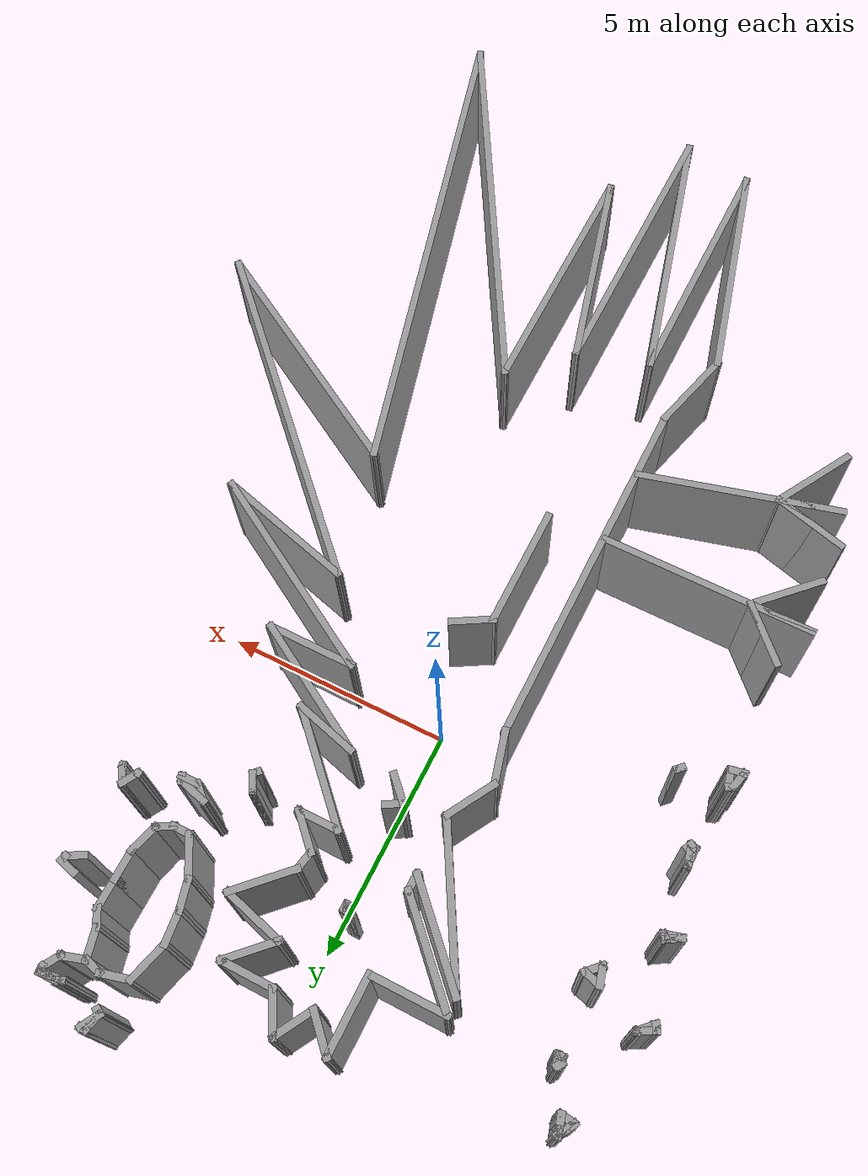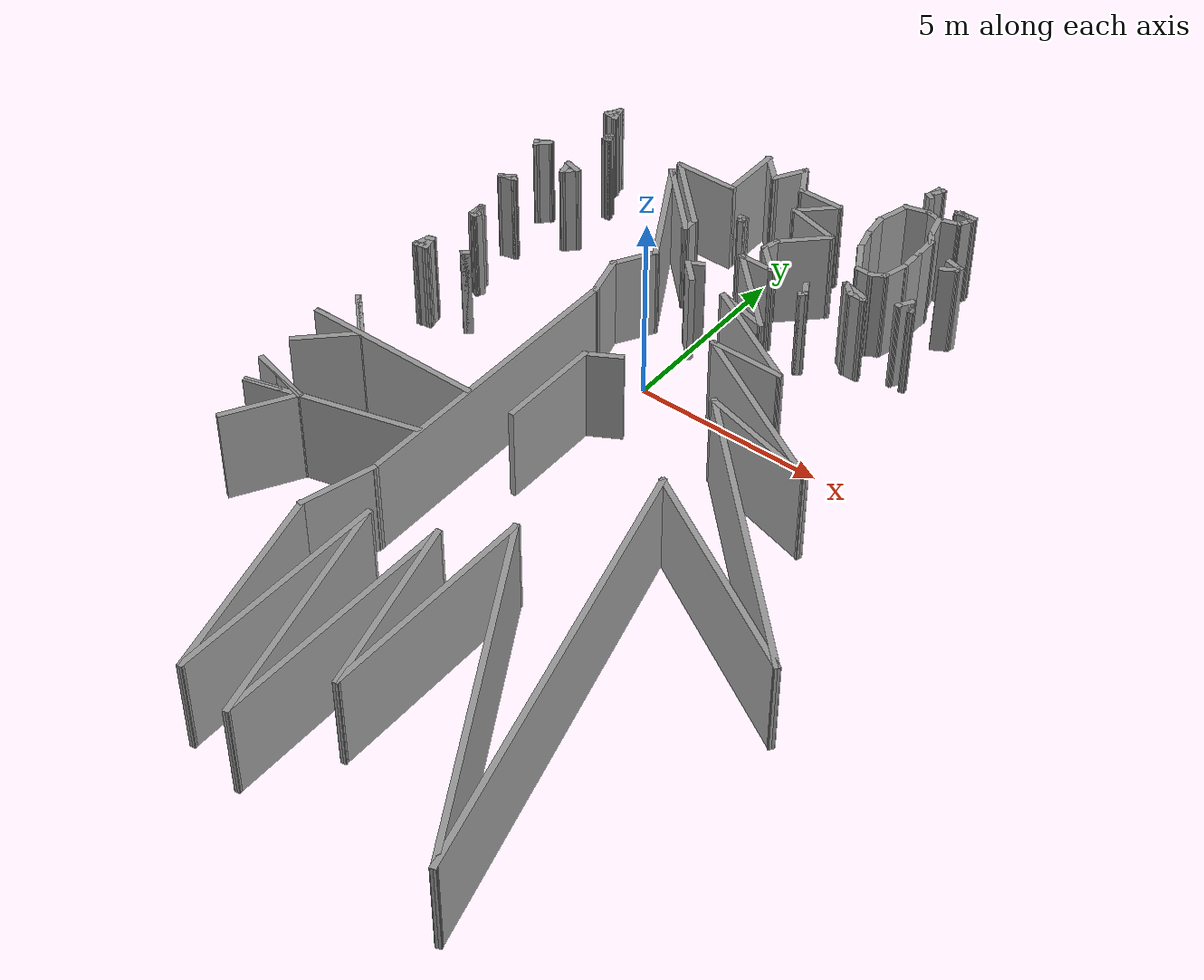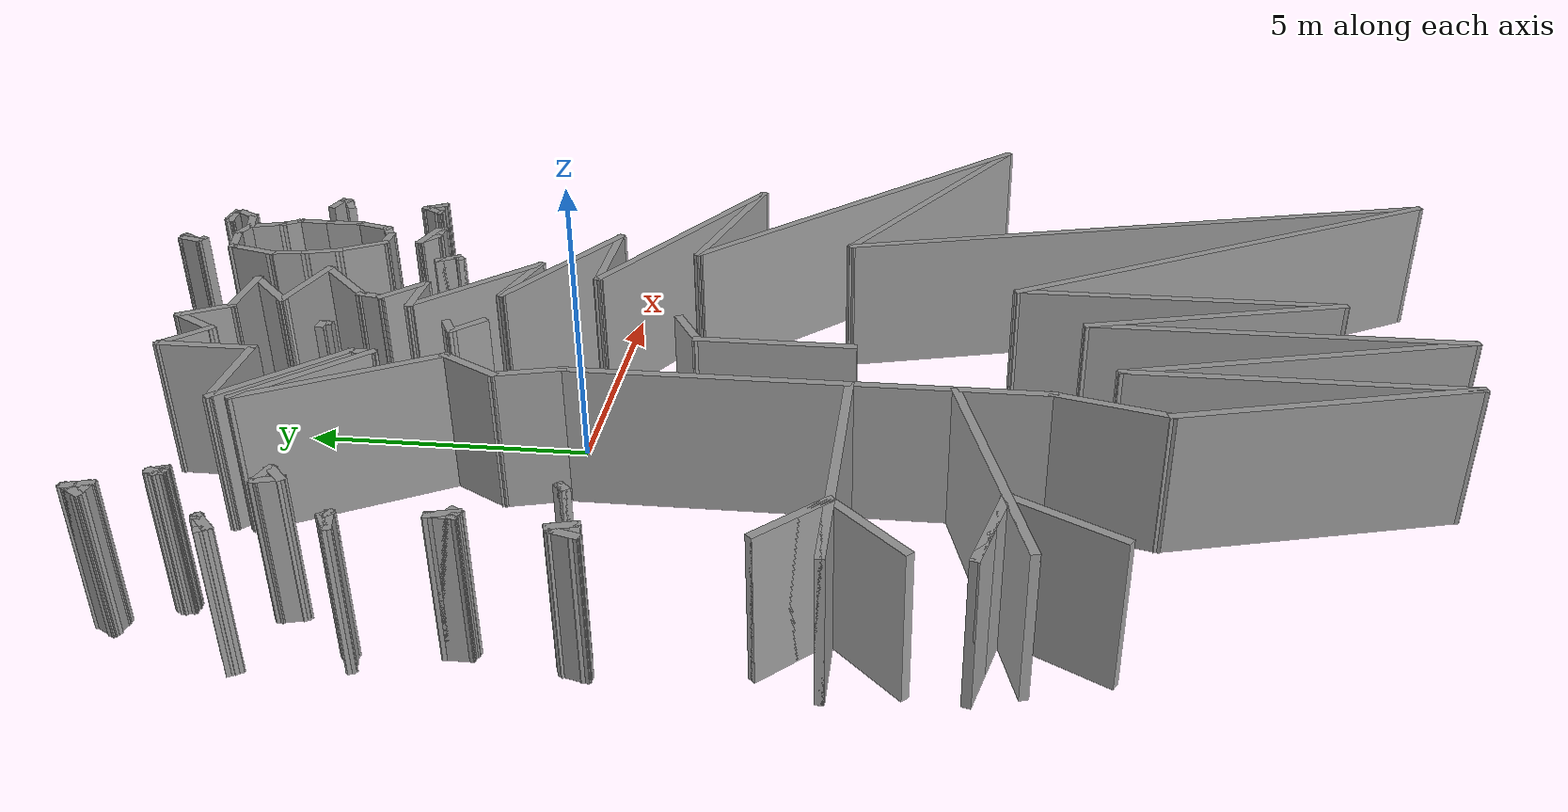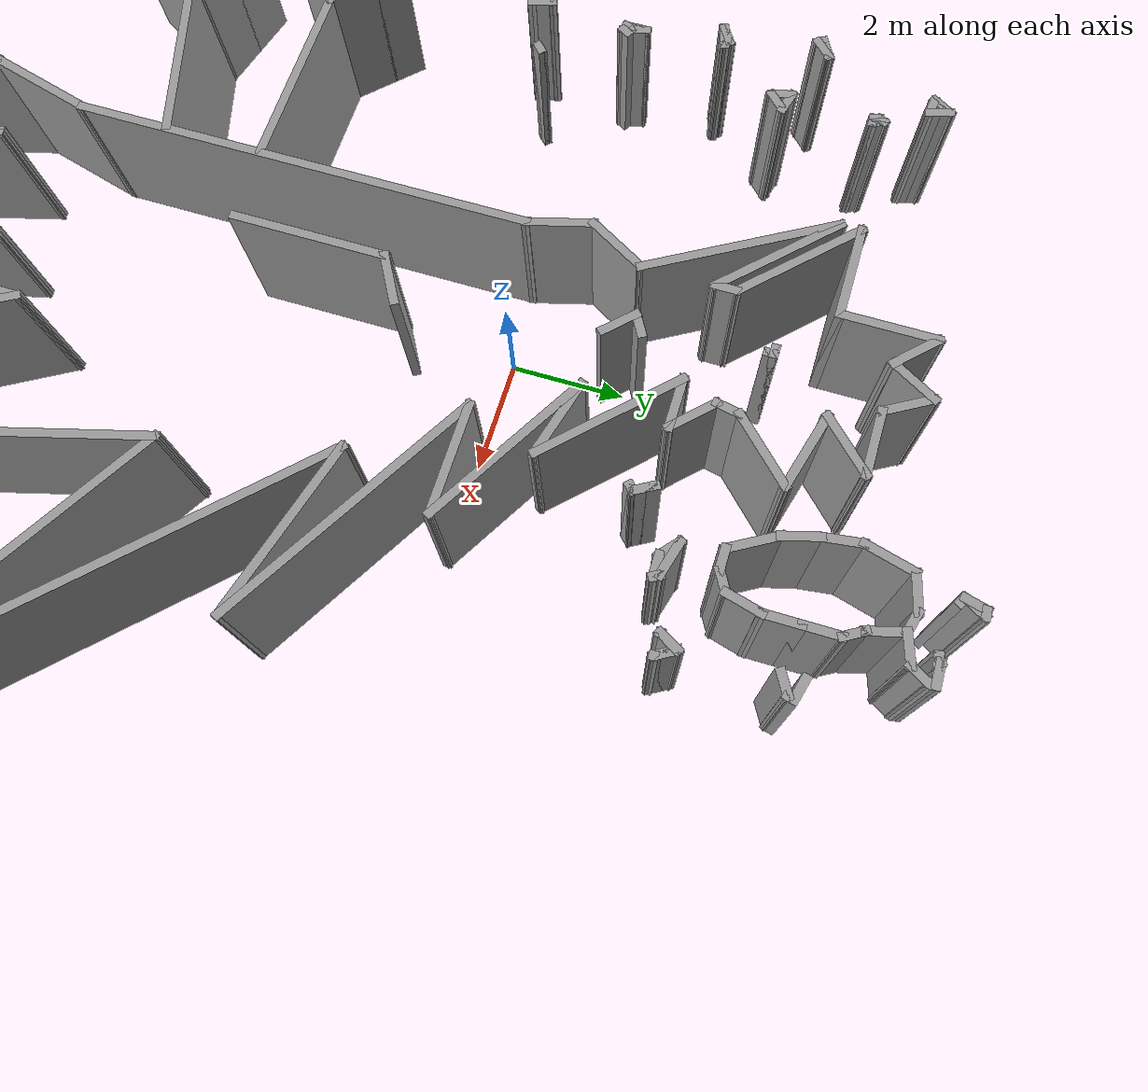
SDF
<?xml version='1.0'?>
<sdf version='1.6'>
  <model name='phenix'>
    <pose frame=''>1.26432 -3.5 0 0 -0 4.71</pose>
    <link name='Wall_1'>
      <collision name='Wall_1_Collision'>
        <geometry>
          <box>
            <size>1.5 0.15 2.5</size>
          </box>
        </geometry>
        <pose frame=''>0 0 1.25 0 -0 0</pose>
      </collision>
      <visual name='Wall_1_Visual'>
        <pose frame=''>0 0 1.25 0 -0 0</pose>
        <geometry>
          <box>
            <size>1.5 0.15 2.5</size>
          </box>
        </geometry>
        <material>
          <script>
            <uri>file://media/materials/scripts/gazebo.material</uri>
            <name>Gazebo/Grey</name>
          </script>
          <ambient>1 1 1 1</ambient>
        </material>
        <meta>
          <layer>0</layer>
        </meta>
      </visual>
      <pose frame=''>-8.07336 0.091289 0 0 -0 2.35619</pose>
    </link>
    <link name='Wall_10'>
      <collision name='Wall_10_Collision'>
        <geometry>
          <box>
            <size>2.5 0.15 2.5</size>
          </box>
        </geometry>
        <pose frame=''>0 0 1.25 0 -0 0</pose>
      </collision>
      <visual name='Wall_10_Visual'>
        <pose frame=''>0 0 1.25 0 -0 0</pose>
        <geometry>
          <box>
            <size>2.5 0.15 2.5</size>
          </box>
        </geometry>
        <material>
          <script>
            <uri>file://media/materials/scripts/gazebo.material</uri>
            <name>Gazebo/Grey</name>
          </script>
          <ambient>1 1 1 1</ambient>
        </material>
        <meta>
          <layer>0</layer>
        </meta>
      </visual>
      <pose frame=''>-7.84807 -3.27779 0 0 -0 0.785398</pose>
    </link>
    <link name='Wall_100'>
      <collision name='Wall_100_Collision'>
        <geometry>
          <box>
            <size>0.5 0.15 2.5</size>
          </box>
        </geometry>
        <pose frame=''>0 0 1.25 0 -0 0</pose>
      </collision>
      <visual name='Wall_100_Visual'>
        <pose frame=''>0 0 1.25 0 -0 0</pose>
        <geometry>
          <box>
            <size>0.5 0.15 2.5</size>
          </box>
        </geometry>
        <material>
          <script>
            <uri>file://media/materials/scripts/gazebo.material</uri>
            <name>Gazebo/Grey</name>
          </script>
          <ambient>1 1 1 1</ambient>
        </material>
        <meta>
          <layer>0</layer>
        </meta>
      </visual>
      <pose frame=''>-7.51869 3.36784 0 0 -0 -0.523599</pose>
    </link>
    <link name='Wall_101'>
      <collision name='Wall_101_Collision'>
        <geometry>
          <box>
            <size>0.15 0.15 2.5</size>
          </box>
        </geometry>
        <pose frame=''>0 0 1.25 0 -0 0</pose>
      </collision>
      <visual name='Wall_101_Visual'>
        <pose frame=''>0 0 1.25 0 -0 0</pose>
        <geometry>
          <box>
            <size>0.15 0.15 2.5</size>
          </box>
        </geometry>
        <material>
          <script>
            <uri>file://media/materials/scripts/gazebo.material</uri>
            <name>Gazebo/Grey</name>
          </script>
          <ambient>1 1 1 1</ambient>
        </material>
        <meta>
          <layer>0</layer>
        </meta>
      </visual>
      <pose frame=''>-7.36714 3.28034 0 0 -0 0</pose>
    </link>
    <link name='Wall_103'>
      <collision name='Wall_103_Collision'>
        <geometry>
          <box>
            <size>0.75 0.15 2.5</size>
          </box>
        </geometry>
        <pose frame=''>0 0 1.25 0 -0 0</pose>
      </collision>
      <visual name='Wall_103_Visual'>
        <pose frame=''>0 0 1.25 0 -0 0</pose>
        <geometry>
          <box>
            <size>0.75 0.15 2.5</size>
          </box>
        </geometry>
        <material>
          <script>
            <uri>file://media/materials/scripts/gazebo.material</uri>
            <name>Gazebo/Grey</name>
          </script>
          <ambient>1 1 1 1</ambient>
        </material>
        <meta>
          <layer>0</layer>
        </meta>
      </visual>
      <pose frame=''>-7.19585 2.15812 0 0 -0 1.309</pose>
    </link>
    <link name='Wall_104'>
      <collision name='Wall_104_Collision'>
        <geometry>
          <box>
            <size>0.25 0.15 2.5</size>
          </box>
        </geometry>
        <pose frame=''>0 0 1.25 0 -0 0</pose>
      </collision>
      <visual name='Wall_104_Visual'>
        <pose frame=''>0 0 1.25 0 -0 0</pose>
        <geometry>
          <box>
            <size>0.25 0.15 2.5</size>
          </box>
        </geometry>
        <material>
          <script>
            <uri>file://media/materials/scripts/gazebo.material</uri>
            <name>Gazebo/Grey</name>
          </script>
          <ambient>1 1 1 1</ambient>
        </material>
        <meta>
          <layer>0</layer>
        </meta>
      </visual>
      <pose frame=''>-7.0749 2.4729 0 0 -0 0.523599</pose>
    </link>
    <link name='Wall_105'>
      <collision name='Wall_105_Collision'>
        <geometry>
          <box>
            <size>0.5 0.15 2.5</size>
          </box>
        </geometry>
        <pose frame=''>0 0 1.25 0 -0 0</pose>
      </collision>
      <visual name='Wall_105_Visual'>
        <pose frame=''>0 0 1.25 0 -0 0</pose>
        <geometry>
          <box>
            <size>0.5 0.15 2.5</size>
          </box>
        </geometry>
        <material>
          <script>
            <uri>file://media/materials/scripts/gazebo.material</uri>
            <name>Gazebo/Grey</name>
          </script>
          <ambient>1 1 1 1</ambient>
        </material>
        <meta>
          <layer>0</layer>
        </meta>
      </visual>
      <pose frame=''>-7.0316 2.3229 0 0 -0 -1.5708</pose>
    </link>
    <link name='Wall_106'>
      <collision name='Wall_106_Collision'>
        <geometry>
          <box>
            <size>0.519681 0.15 2.5</size>
          </box>
        </geometry>
        <pose frame=''>0 0 1.25 0 -0 0</pose>
      </collision>
      <visual name='Wall_106_Visual'>
        <pose frame=''>0 0 1.25 0 -0 0</pose>
        <geometry>
          <box>
            <size>0.519681 0.15 2.5</size>
          </box>
        </geometry>
        <material>
          <script>
            <uri>file://media/materials/scripts/gazebo.material</uri>
            <name>Gazebo/Grey</name>
          </script>
          <ambient>1 1 1 1</ambient>
        </material>
        <meta>
          <layer>0</layer>
        </meta>
      </visual>
      <pose frame=''>-7.15255 2.00812 0 0 -0 -2.2841</pose>
    </link>
    <link name='Wall_108'>
      <collision name='Wall_108_Collision'>
        <geometry>
          <box>
            <size>0.5 0.15 2.5</size>
          </box>
        </geometry>
        <pose frame=''>0 0 1.25 0 -0 0</pose>
      </collision>
      <visual name='Wall_108_Visual'>
        <pose frame=''>0 0 1.25 0 -0 0</pose>
        <geometry>
          <box>
            <size>0.5 0.15 2.5</size>
          </box>
        </geometry>
        <material>
          <script>
            <uri>file://media/materials/scripts/gazebo.material</uri>
            <name>Gazebo/Grey</name>
          </script>
          <ambient>1 1 1 1</ambient>
        </material>
        <meta>
          <layer>0</layer>
        </meta>
      </visual>
      <pose frame=''>-6.52682 1.20202 0 0 -0 0.523599</pose>
    </link>
    <link name='Wall_109'>
      <collision name='Wall_109_Collision'>
        <geometry>
          <box>
            <size>0.25 0.15 2.5</size>
          </box>
        </geometry>
        <pose frame=''>0 0 1.25 0 -0 0</pose>
      </collision>
      <visual name='Wall_109_Visual'>
        <pose frame=''>0 0 1.25 0 -0 0</pose>
        <geometry>
          <box>
            <size>0.25 0.15 2.5</size>
          </box>
        </geometry>
        <material>
          <script>
            <uri>file://media/materials/scripts/gazebo.material</uri>
            <name>Gazebo/Grey</name>
          </script>
          <ambient>1 1 1 1</ambient>
        </material>
        <meta>
          <layer>0</layer>
        </meta>
      </visual>
      <pose frame=''>-6.33991 1.25416 0 0 -0 -0.785398</pose>
    </link>
    <link name='Wall_11'>
      <collision name='Wall_11_Collision'>
        <geometry>
          <box>
            <size>0.5 0.15 2.5</size>
          </box>
        </geometry>
        <pose frame=''>0 0 1.25 0 -0 0</pose>
      </collision>
      <visual name='Wall_11_Visual'>
        <pose frame=''>0 0 1.25 0 -0 0</pose>
        <geometry>
          <box>
            <size>0.5 0.15 2.5</size>
          </box>
        </geometry>
        <material>
          <script>
            <uri>file://media/materials/scripts/gazebo.material</uri>
            <name>Gazebo/Grey</name>
          </script>
          <ambient>1 1 1 1</ambient>
        </material>
        <meta>
          <layer>0</layer>
        </meta>
      </visual>
      <pose frame=''>-6.84222 -2.44694 0 0 -0 0</pose>
    </link>
    <link name='Wall_110'>
      <collision name='Wall_110_Collision'>
        <geometry>
          <box>
            <size>0.25 0.15 2.5</size>
          </box>
        </geometry>
        <pose frame=''>0 0 1.25 0 -0 0</pose>
      </collision>
      <visual name='Wall_110_Visual'>
        <pose frame=''>0 0 1.25 0 -0 0</pose>
        <geometry>
          <box>
            <size>0.25 0.15 2.5</size>
          </box>
        </geometry>
        <material>
          <script>
            <uri>file://media/materials/scripts/gazebo.material</uri>
            <name>Gazebo/Grey</name>
          </script>
          <ambient>1 1 1 1</ambient>
        </material>
        <meta>
          <layer>0</layer>
        </meta>
      </visual>
      <pose frame=''>-6.33991 1.25416 0 0 -0 2.35619</pose>
    </link>
    <link name='Wall_111'>
      <collision name='Wall_111_Collision'>
        <geometry>
          <box>
            <size>0.5 0.15 2.5</size>
          </box>
        </geometry>
        <pose frame=''>0 0 1.25 0 -0 0</pose>
      </collision>
      <visual name='Wall_111_Visual'>
        <pose frame=''>0 0 1.25 0 -0 0</pose>
        <geometry>
          <box>
            <size>0.5 0.15 2.5</size>
          </box>
        </geometry>
        <material>
          <script>
            <uri>file://media/materials/scripts/gazebo.material</uri>
            <name>Gazebo/Grey</name>
          </script>
          <ambient>1 1 1 1</ambient>
        </material>
        <meta>
          <layer>0</layer>
        </meta>
      </visual>
      <pose frame=''>-6.52682 1.20202 0 0 -0 -2.61799</pose>
    </link>
    <link name='Wall_112'>
      <collision name='Wall_112_Collision'>
        <geometry>
          <box>
            <size>0.5 0.15 2.5</size>
          </box>
        </geometry>
        <pose frame=''>0 0 1.25 0 -0 0</pose>
      </collision>
      <visual name='Wall_112_Visual'>
        <pose frame=''>0 0 1.25 0 -0 0</pose>
        <geometry>
          <box>
            <size>0.5 0.15 2.5</size>
          </box>
        </geometry>
        <material>
          <script>
            <uri>file://media/materials/scripts/gazebo.material</uri>
            <name>Gazebo/Grey</name>
          </script>
          <ambient>1 1 1 1</ambient>
        </material>
        <meta>
          <layer>0</layer>
        </meta>
      </visual>
      <pose frame=''>-6.52682 1.20202 0 0 -0 0.523599</pose>
    </link>
    <link name='Wall_115'>
      <collision name='Wall_115_Collision'>
        <geometry>
          <box>
            <size>0.25 0.15 2.5</size>
          </box>
        </geometry>
        <pose frame=''>0 0 1.25 0 -0 0</pose>
      </collision>
      <visual name='Wall_115_Visual'>
        <pose frame=''>0 0 1.25 0 -0 0</pose>
        <geometry>
          <box>
            <size>0.25 0.15 2.5</size>
          </box>
        </geometry>
        <material>
          <script>
            <uri>file://media/materials/scripts/gazebo.material</uri>
            <name>Gazebo/Grey</name>
          </script>
          <ambient>1 1 1 1</ambient>
        </material>
        <meta>
          <layer>0</layer>
        </meta>
      </visual>
      <pose frame=''>-9.55478 -6.74044 0 0 -0 0.261799</pose>
    </link>
    <link name='Wall_116'>
      <collision name='Wall_116_Collision'>
        <geometry>
          <box>
            <size>0.25 0.15 2.5</size>
          </box>
        </geometry>
        <pose frame=''>0 0 1.25 0 -0 0</pose>
      </collision>
      <visual name='Wall_116_Visual'>
        <pose frame=''>0 0 1.25 0 -0 0</pose>
        <geometry>
          <box>
            <size>0.25 0.15 2.5</size>
          </box>
        </geometry>
        <material>
          <script>
            <uri>file://media/materials/scripts/gazebo.material</uri>
            <name>Gazebo/Grey</name>
          </script>
          <ambient>1 1 1 1</ambient>
        </material>
        <meta>
          <layer>0</layer>
        </meta>
      </visual>
      <pose frame=''>-9.55478 -6.74044 0 0 -0 -2.87979</pose>
    </link>
    <link name='Wall_117'>
      <collision name='Wall_117_Collision'>
        <geometry>
          <box>
            <size>0.25 0.15 2.5</size>
          </box>
        </geometry>
        <pose frame=''>0 0 1.25 0 -0 0</pose>
      </collision>
      <visual name='Wall_117_Visual'>
        <pose frame=''>0 0 1.25 0 -0 0</pose>
        <geometry>
          <box>
            <size>0.25 0.15 2.5</size>
          </box>
        </geometry>
        <material>
          <script>
            <uri>file://media/materials/scripts/gazebo.material</uri>
            <name>Gazebo/Grey</name>
          </script>
          <ambient>1 1 1 1</ambient>
        </material>
        <meta>
          <layer>0</layer>
        </meta>
      </visual>
      <pose frame=''>-9.55478 -6.74044 0 0 -0 0.261799</pose>
    </link>
    <link name='Wall_118'>
      <collision name='Wall_118_Collision'>
        <geometry>
          <box>
            <size>0.25 0.15 2.5</size>
          </box>
        </geometry>
        <pose frame=''>0 0 1.25 0 -0 0</pose>
      </collision>
      <visual name='Wall_118_Visual'>
        <pose frame=''>0 0 1.25 0 -0 0</pose>
        <geometry>
          <box>
            <size>0.25 0.15 2.5</size>
          </box>
        </geometry>
        <material>
          <script>
            <uri>file://media/materials/scripts/gazebo.material</uri>
            <name>Gazebo/Grey</name>
          </script>
          <ambient>1 1 1 1</ambient>
        </material>
        <meta>
          <layer>0</layer>
        </meta>
      </visual>
      <pose frame=''>-9.55478 -6.74044 0 0 -0 -2.87979</pose>
    </link>
    <link name='Wall_119'>
      <collision name='Wall_119_Collision'>
        <geometry>
          <box>
            <size>0.5 0.15 2.5</size>
          </box>
        </geometry>
        <pose frame=''>0 0 1.25 0 -0 0</pose>
      </collision>
      <visual name='Wall_119_Visual'>
        <pose frame=''>0 0 1.25 0 -0 0</pose>
        <geometry>
          <box>
            <size>0.5 0.15 2.5</size>
          </box>
        </geometry>
        <material>
          <script>
            <uri>file://media/materials/scripts/gazebo.material</uri>
            <name>Gazebo/Grey</name>
          </script>
          <ambient>1 1 1 1</ambient>
        </material>
        <meta>
          <layer>0</layer>
        </meta>
      </visual>
      <pose frame=''>-9.45152 -6.84088 0 0 -0 -0.523599</pose>
    </link>
    <link name='Wall_12'>
      <collision name='Wall_12_Collision'>
        <geometry>
          <box>
            <size>2.5 0.15 2.5</size>
          </box>
        </geometry>
        <pose frame=''>0 0 1.25 0 -0 0</pose>
      </collision>
      <visual name='Wall_12_Visual'>
        <pose frame=''>0 0 1.25 0 -0 0</pose>
        <geometry>
          <box>
            <size>2.5 0.15 2.5</size>
          </box>
        </geometry>
        <material>
          <script>
            <uri>file://media/materials/scripts/gazebo.material</uri>
            <name>Gazebo/Grey</name>
          </script>
          <ambient>1 1 1 1</ambient>
        </material>
        <meta>
          <layer>0</layer>
        </meta>
      </visual>
      <pose frame=''>-7.49807 -3.27779 0 0 -0 -2.35619</pose>
    </link>
    <link name='Wall_120'>
      <collision name='Wall_120_Collision'>
        <geometry>
          <box>
            <size>0.5 0.15 2.5</size>
          </box>
        </geometry>
        <pose frame=''>0 0 1.25 0 -0 0</pose>
      </collision>
      <visual name='Wall_120_Visual'>
        <pose frame=''>0 0 1.25 0 -0 0</pose>
        <geometry>
          <box>
            <size>0.5 0.15 2.5</size>
          </box>
        </geometry>
        <material>
          <script>
            <uri>file://media/materials/scripts/gazebo.material</uri>
            <name>Gazebo/Grey</name>
          </script>
          <ambient>1 1 1 1</ambient>
        </material>
        <meta>
          <layer>0</layer>
        </meta>
      </visual>
      <pose frame=''>-9.45152 -6.84088 0 0 -0 2.61799</pose>
    </link>
    <link name='Wall_121'>
      <collision name='Wall_121_Collision'>
        <geometry>
          <box>
            <size>0.5 0.15 2.5</size>
          </box>
        </geometry>
        <pose frame=''>0 0 1.25 0 -0 0</pose>
      </collision>
      <visual name='Wall_121_Visual'>
        <pose frame=''>0 0 1.25 0 -0 0</pose>
        <geometry>
          <box>
            <size>0.5 0.15 2.5</size>
          </box>
        </geometry>
        <material>
          <script>
            <uri>file://media/materials/scripts/gazebo.material</uri>
            <name>Gazebo/Grey</name>
          </script>
          <ambient>1 1 1 1</ambient>
        </material>
        <meta>
          <layer>0</layer>
        </meta>
      </visual>
      <pose frame=''>-9.43404 -6.70809 0 0 -0 0.261799</pose>
    </link>
    <link name='Wall_122'>
      <collision name='Wall_122_Collision'>
        <geometry>
          <box>
            <size>0.417878 0.15 2.5</size>
          </box>
        </geometry>
        <pose frame=''>0 0 1.25 0 -0 0</pose>
      </collision>
      <visual name='Wall_122_Visual'>
        <pose frame=''>0 0 1.25 0 -0 0</pose>
        <geometry>
          <box>
            <size>0.417878 0.15 2.5</size>
          </box>
        </geometry>
        <material>
          <script>
            <uri>file://media/materials/scripts/gazebo.material</uri>
            <name>Gazebo/Grey</name>
          </script>
          <ambient>1 1 1 1</ambient>
        </material>
        <meta>
          <layer>0</layer>
        </meta>
      </visual>
      <pose frame=''>-9.28248 -6.79559 0 0 -0 -1.7017</pose>
    </link>
    <link name='Wall_124'>
      <collision name='Wall_124_Collision'>
        <geometry>
          <box>
            <size>0.25 0.15 2.5</size>
          </box>
        </geometry>
        <pose frame=''>0 0 1.25 0 -0 0</pose>
      </collision>
      <visual name='Wall_124_Visual'>
        <pose frame=''>0 0 1.25 0 -0 0</pose>
        <geometry>
          <box>
            <size>0.25 0.15 2.5</size>
          </box>
        </geometry>
        <material>
          <script>
            <uri>file://media/materials/scripts/gazebo.material</uri>
            <name>Gazebo/Grey</name>
          </script>
          <ambient>1 1 1 1</ambient>
        </material>
        <meta>
          <layer>0</layer>
        </meta>
      </visual>
      <pose frame=''>-8.53062 -6.28095 0 0 -0 -0.523599</pose>
    </link>
    <link name='Wall_125'>
      <collision name='Wall_125_Collision'>
        <geometry>
          <box>
            <size>0.25 0.15 2.5</size>
          </box>
        </geometry>
        <pose frame=''>0 0 1.25 0 -0 0</pose>
      </collision>
      <visual name='Wall_125_Visual'>
        <pose frame=''>0 0 1.25 0 -0 0</pose>
        <geometry>
          <box>
            <size>0.25 0.15 2.5</size>
          </box>
        </geometry>
        <material>
          <script>
            <uri>file://media/materials/scripts/gazebo.material</uri>
            <name>Gazebo/Grey</name>
          </script>
          <ambient>1 1 1 1</ambient>
        </material>
        <meta>
          <layer>0</layer>
        </meta>
      </visual>
      <pose frame=''>-8.43902 -6.29301 0 0 -0 0.261799</pose>
    </link>
    <link name='Wall_126'>
      <collision name='Wall_126_Collision'>
        <geometry>
          <box>
            <size>0.15 0.15 2.5</size>
          </box>
        </geometry>
        <pose frame=''>0 0 1.25 0 -0 0</pose>
      </collision>
      <visual name='Wall_126_Visual'>
        <pose frame=''>0 0 1.25 0 -0 0</pose>
        <geometry>
          <box>
            <size>0.15 0.15 2.5</size>
          </box>
        </geometry>
        <material>
          <script>
            <uri>file://media/materials/scripts/gazebo.material</uri>
            <name>Gazebo/Grey</name>
          </script>
          <ambient>1 1 1 1</ambient>
        </material>
        <meta>
          <layer>0</layer>
        </meta>
      </visual>
      <pose frame=''>-8.39072 -6.28007 0 0 -0 0</pose>
    </link>
    <link name='Wall_127'>
      <collision name='Wall_127_Collision'>
        <geometry>
          <box>
            <size>0.25 0.15 2.5</size>
          </box>
        </geometry>
        <pose frame=''>0 0 1.25 0 -0 0</pose>
      </collision>
      <visual name='Wall_127_Visual'>
        <pose frame=''>0 0 1.25 0 -0 0</pose>
        <geometry>
          <box>
            <size>0.25 0.15 2.5</size>
          </box>
        </geometry>
        <material>
          <script>
            <uri>file://media/materials/scripts/gazebo.material</uri>
            <name>Gazebo/Grey</name>
          </script>
          <ambient>1 1 1 1</ambient>
        </material>
        <meta>
          <layer>0</layer>
        </meta>
      </visual>
      <pose frame=''>-8.39072 -6.23007 0 0 -0 1.5708</pose>
    </link>
    <link name='Wall_128'>
      <collision name='Wall_128_Collision'>
        <geometry>
          <box>
            <size>0.25 0.15 2.5</size>
          </box>
        </geometry>
        <pose frame=''>0 0 1.25 0 -0 0</pose>
      </collision>
      <visual name='Wall_128_Visual'>
        <pose frame=''>0 0 1.25 0 -0 0</pose>
        <geometry>
          <box>
            <size>0.25 0.15 2.5</size>
          </box>
        </geometry>
        <material>
          <script>
            <uri>file://media/materials/scripts/gazebo.material</uri>
            <name>Gazebo/Grey</name>
          </script>
          <ambient>1 1 1 1</ambient>
        </material>
        <meta>
          <layer>0</layer>
        </meta>
      </visual>
      <pose frame=''>-8.39072 -6.23007 0 0 -0 -1.5708</pose>
    </link>
    <link name='Wall_129'>
      <collision name='Wall_129_Collision'>
        <geometry>
          <box>
            <size>0.334776 0.15 2.5</size>
          </box>
        </geometry>
        <pose frame=''>0 0 1.25 0 -0 0</pose>
      </collision>
      <visual name='Wall_129_Visual'>
        <pose frame=''>0 0 1.25 0 -0 0</pose>
        <geometry>
          <box>
            <size>0.334776 0.15 2.5</size>
          </box>
        </geometry>
        <material>
          <script>
            <uri>file://media/materials/scripts/gazebo.material</uri>
            <name>Gazebo/Grey</name>
          </script>
          <ambient>1 1 1 1</ambient>
        </material>
        <meta>
          <layer>0</layer>
        </meta>
      </visual>
      <pose frame=''>-8.48232 -6.26801 0 0 -0 3.01069</pose>
    </link>
    <link name='Wall_13'>
      <collision name='Wall_13_Collision'>
        <geometry>
          <box>
            <size>3.5 0.15 2.5</size>
          </box>
        </geometry>
        <pose frame=''>0 0 1.25 0 -0 0</pose>
      </collision>
      <visual name='Wall_13_Visual'>
        <pose frame=''>0 0 1.25 0 -0 0</pose>
        <geometry>
          <box>
            <size>3.5 0.15 2.5</size>
          </box>
        </geometry>
        <material>
          <script>
            <uri>file://media/materials/scripts/gazebo.material</uri>
            <name>Gazebo/Grey</name>
          </script>
          <ambient>1 1 1 1</ambient>
        </material>
        <meta>
          <layer>0</layer>
        </meta>
      </visual>
      <pose frame=''>-6.87833 -3.27114 0 0 -0 0.523599</pose>
    </link>
    <link name='Wall_130'>
      <collision name='Wall_130_Collision'>
        <geometry>
          <box>
            <size>0.348289 0.15 2.5</size>
          </box>
        </geometry>
        <pose frame=''>0 0 1.25 0 -0 0</pose>
      </collision>
      <visual name='Wall_130_Visual'>
        <pose frame=''>0 0 1.25 0 -0 0</pose>
        <geometry>
          <box>
            <size>0.348289 0.15 2.5</size>
          </box>
        </geometry>
        <material>
          <script>
            <uri>file://media/materials/scripts/gazebo.material</uri>
            <name>Gazebo/Grey</name>
          </script>
          <ambient>1 1 1 1</ambient>
        </material>
        <meta>
          <layer>0</layer>
        </meta>
      </visual>
      <pose frame=''>-8.48232 -6.21801 0 0 -0 0.392699</pose>
    </link>
    <link name='Wall_132'>
      <collision name='Wall_132_Collision'>
        <geometry>
          <box>
            <size>0.25 0.15 2.5</size>
          </box>
        </geometry>
        <pose frame=''>0 0 1.25 0 -0 0</pose>
      </collision>
      <visual name='Wall_132_Visual'>
        <pose frame=''>0 0 1.25 0 -0 0</pose>
        <geometry>
          <box>
            <size>0.25 0.15 2.5</size>
          </box>
        </geometry>
        <material>
          <script>
            <uri>file://media/materials/scripts/gazebo.material</uri>
            <name>Gazebo/Grey</name>
          </script>
          <ambient>1 1 1 1</ambient>
        </material>
        <meta>
          <layer>0</layer>
        </meta>
      </visual>
      <pose frame=''>-7.17556 -7.56886 0 0 -0 0.523599</pose>
    </link>
    <link name='Wall_133'>
      <collision name='Wall_133_Collision'>
        <geometry>
          <box>
            <size>0.5 0.15 2.5</size>
          </box>
        </geometry>
        <pose frame=''>0 0 1.25 0 -0 0</pose>
      </collision>
      <visual name='Wall_133_Visual'>
        <pose frame=''>0 0 1.25 0 -0 0</pose>
        <geometry>
          <box>
            <size>0.5 0.15 2.5</size>
          </box>
        </geometry>
        <material>
          <script>
            <uri>file://media/materials/scripts/gazebo.material</uri>
            <name>Gazebo/Grey</name>
          </script>
          <ambient>1 1 1 1</ambient>
        </material>
        <meta>
          <layer>0</layer>
        </meta>
      </visual>
      <pose frame=''>-7.25601 -7.42011 0 0 -0 2.35619</pose>
    </link>
    <link name='Wall_134'>
      <collision name='Wall_134_Collision'>
        <geometry>
          <box>
            <size>0.15 0.15 2.5</size>
          </box>
        </geometry>
        <pose frame=''>0 0 1.25 0 -0 0</pose>
      </collision>
      <visual name='Wall_134_Visual'>
        <pose frame=''>0 0 1.25 0 -0 0</pose>
        <geometry>
          <box>
            <size>0.15 0.15 2.5</size>
          </box>
        </geometry>
        <material>
          <script>
            <uri>file://media/materials/scripts/gazebo.material</uri>
            <name>Gazebo/Grey</name>
          </script>
          <ambient>1 1 1 1</ambient>
        </material>
        <meta>
          <layer>0</layer>
        </meta>
      </visual>
      <pose frame=''>-7.37975 -7.29637 0 0 -0 0</pose>
    </link>
    <link name='Wall_135'>
      <collision name='Wall_135_Collision'>
        <geometry>
          <box>
            <size>0.488205 0.15 2.5</size>
          </box>
        </geometry>
        <pose frame=''>0 0 1.25 0 -0 0</pose>
      </collision>
      <visual name='Wall_135_Visual'>
        <pose frame=''>0 0 1.25 0 -0 0</pose>
        <geometry>
          <box>
            <size>0.488205 0.15 2.5</size>
          </box>
        </geometry>
        <material>
          <script>
            <uri>file://media/materials/scripts/gazebo.material</uri>
            <name>Gazebo/Grey</name>
          </script>
          <ambient>1 1 1 1</ambient>
        </material>
        <meta>
          <layer>0</layer>
        </meta>
      </visual>
      <pose frame=''>-7.29931 -7.44511 0 0 -0 -1.07503</pose>
    </link>
    <link name='Wall_137'>
      <collision name='Wall_137_Collision'>
        <geometry>
          <box>
            <size>0.5 0.15 2.5</size>
          </box>
        </geometry>
        <pose frame=''>0 0 1.25 0 -0 0</pose>
      </collision>
      <visual name='Wall_137_Visual'>
        <pose frame=''>0 0 1.25 0 -0 0</pose>
        <geometry>
          <box>
            <size>0.5 0.15 2.5</size>
          </box>
        </geometry>
        <material>
          <script>
            <uri>file://media/materials/scripts/gazebo.material</uri>
            <name>Gazebo/Grey</name>
          </script>
          <ambient>1 1 1 1</ambient>
        </material>
        <meta>
          <layer>0</layer>
        </meta>
      </visual>
      <pose frame=''>-6.75207 -6.13956 0 0 -0 -0.785398</pose>
    </link>
    <link name='Wall_138'>
      <collision name='Wall_138_Collision'>
        <geometry>
          <box>
            <size>0.5 0.15 2.5</size>
          </box>
        </geometry>
        <pose frame=''>0 0 1.25 0 -0 0</pose>
      </collision>
      <visual name='Wall_138_Visual'>
        <pose frame=''>0 0 1.25 0 -0 0</pose>
        <geometry>
          <box>
            <size>0.5 0.15 2.5</size>
          </box>
        </geometry>
        <material>
          <script>
            <uri>file://media/materials/scripts/gazebo.material</uri>
            <name>Gazebo/Grey</name>
          </script>
          <ambient>1 1 1 1</ambient>
        </material>
        <meta>
          <layer>0</layer>
        </meta>
      </visual>
      <pose frame=''>-6.79736 -6.3086 0 0 -0 -2.87979</pose>
    </link>
    <link name='Wall_139'>
      <collision name='Wall_139_Collision'>
        <geometry>
          <box>
            <size>0.5 0.15 2.5</size>
          </box>
        </geometry>
        <pose frame=''>0 0 1.25 0 -0 0</pose>
      </collision>
      <visual name='Wall_139_Visual'>
        <pose frame=''>0 0 1.25 0 -0 0</pose>
        <geometry>
          <box>
            <size>0.5 0.15 2.5</size>
          </box>
        </geometry>
        <material>
          <script>
            <uri>file://media/materials/scripts/gazebo.material</uri>
            <name>Gazebo/Grey</name>
          </script>
          <ambient>1 1 1 1</ambient>
        </material>
        <meta>
          <layer>0</layer>
        </meta>
      </visual>
      <pose frame=''>-6.92111 -6.18485 0 0 -0 1.309</pose>
    </link>
    <link name='Wall_14'>
      <collision name='Wall_14_Collision'>
        <geometry>
          <box>
            <size>1.25 0.15 2.5</size>
          </box>
        </geometry>
        <pose frame=''>0 0 1.25 0 -0 0</pose>
      </collision>
      <visual name='Wall_14_Visual'>
        <pose frame=''>0 0 1.25 0 -0 0</pose>
        <geometry>
          <box>
            <size>1.25 0.15 2.5</size>
          </box>
        </geometry>
        <material>
          <script>
            <uri>file://media/materials/scripts/gazebo.material</uri>
            <name>Gazebo/Grey</name>
          </script>
          <ambient>1 1 1 1</ambient>
        </material>
        <meta>
          <layer>0</layer>
        </meta>
      </visual>
      <pose frame=''>-4.95142 -2.70864 0 0 -0 -0.523599</pose>
    </link>
    <link name='Wall_141'>
      <collision name='Wall_141_Collision'>
        <geometry>
          <box>
            <size>0.25 0.15 2.5</size>
          </box>
        </geometry>
        <pose frame=''>0 0 1.25 0 -0 0</pose>
      </collision>
      <visual name='Wall_141_Visual'>
        <pose frame=''>0 0 1.25 0 -0 0</pose>
        <geometry>
          <box>
            <size>0.25 0.15 2.5</size>
          </box>
        </geometry>
        <material>
          <script>
            <uri>file://media/materials/scripts/gazebo.material</uri>
            <name>Gazebo/Grey</name>
          </script>
          <ambient>1 1 1 1</ambient>
        </material>
        <meta>
          <layer>0</layer>
        </meta>
      </visual>
      <pose frame=''>-5.64188 -7.06318 0 0 -0 -2.35619</pose>
    </link>
    <link name='Wall_142'>
      <collision name='Wall_142_Collision'>
        <geometry>
          <box>
            <size>0.25 0.15 2.5</size>
          </box>
        </geometry>
        <pose frame=''>0 0 1.25 0 -0 0</pose>
      </collision>
      <visual name='Wall_142_Visual'>
        <pose frame=''>0 0 1.25 0 -0 0</pose>
        <geometry>
          <box>
            <size>0.25 0.15 2.5</size>
          </box>
        </geometry>
        <material>
          <script>
            <uri>file://media/materials/scripts/gazebo.material</uri>
            <name>Gazebo/Grey</name>
          </script>
          <ambient>1 1 1 1</ambient>
        </material>
        <meta>
          <layer>0</layer>
        </meta>
      </visual>
      <pose frame=''>-5.64188 -7.06318 0 0 -0 0.785398</pose>
    </link>
    <link name='Wall_143'>
      <collision name='Wall_143_Collision'>
        <geometry>
          <box>
            <size>0.5 0.15 2.5</size>
          </box>
        </geometry>
        <pose frame=''>0 0 1.25 0 -0 0</pose>
      </collision>
      <visual name='Wall_143_Visual'>
        <pose frame=''>0 0 1.25 0 -0 0</pose>
        <geometry>
          <box>
            <size>0.5 0.15 2.5</size>
          </box>
        </geometry>
        <material>
          <script>
            <uri>file://media/materials/scripts/gazebo.material</uri>
            <name>Gazebo/Grey</name>
          </script>
          <ambient>1 1 1 1</ambient>
        </material>
        <meta>
          <layer>0</layer>
        </meta>
      </visual>
      <pose frame=''>-5.56123 -7.19686 0 0 -0 -1.309</pose>
    </link>
    <link name='Wall_144'>
      <collision name='Wall_144_Collision'>
        <geometry>
          <box>
            <size>0.46225 0.15 2.5</size>
          </box>
        </geometry>
        <pose frame=''>0 0 1.25 0 -0 0</pose>
      </collision>
      <visual name='Wall_144_Visual'>
        <pose frame=''>0 0 1.25 0 -0 0</pose>
        <geometry>
          <box>
            <size>0.46225 0.15 2.5</size>
          </box>
        </geometry>
        <material>
          <script>
            <uri>file://media/materials/scripts/gazebo.material</uri>
            <name>Gazebo/Grey</name>
          </script>
          <ambient>1 1 1 1</ambient>
        </material>
        <meta>
          <layer>0</layer>
        </meta>
      </visual>
      <pose frame=''>-5.59658 -7.23221 0 0 -0 2.11363</pose>
    </link>
    <link name='Wall_146'>
      <collision name='Wall_146_Collision'>
        <geometry>
          <box>
            <size>0.25 0.15 2.5</size>
          </box>
        </geometry>
        <pose frame=''>0 0 1.25 0 -0 0</pose>
      </collision>
      <visual name='Wall_146_Visual'>
        <pose frame=''>0 0 1.25 0 -0 0</pose>
        <geometry>
          <box>
            <size>0.25 0.15 2.5</size>
          </box>
        </geometry>
        <material>
          <script>
            <uri>file://media/materials/scripts/gazebo.material</uri>
            <name>Gazebo/Grey</name>
          </script>
          <ambient>1 1 1 1</ambient>
        </material>
        <meta>
          <layer>0</layer>
        </meta>
      </visual>
      <pose frame=''>-3.89942 -6.81269 0 0 -0 -0.523599</pose>
    </link>
    <link name='Wall_147'>
      <collision name='Wall_147_Collision'>
        <geometry>
          <box>
            <size>0.25 0.15 2.5</size>
          </box>
        </geometry>
        <pose frame=''>0 0 1.25 0 -0 0</pose>
      </collision>
      <visual name='Wall_147_Visual'>
        <pose frame=''>0 0 1.25 0 -0 0</pose>
        <geometry>
          <box>
            <size>0.25 0.15 2.5</size>
          </box>
        </geometry>
        <material>
          <script>
            <uri>file://media/materials/scripts/gazebo.material</uri>
            <name>Gazebo/Grey</name>
          </script>
          <ambient>1 1 1 1</ambient>
        </material>
        <meta>
          <layer>0</layer>
        </meta>
      </visual>
      <pose frame=''>-3.86906 -6.88598 0 0 -0 -1.8326</pose>
    </link>
    <link name='Wall_148'>
      <collision name='Wall_148_Collision'>
        <geometry>
          <box>
            <size>0.5 0.15 2.5</size>
          </box>
        </geometry>
        <pose frame=''>0 0 1.25 0 -0 0</pose>
      </collision>
      <visual name='Wall_148_Visual'>
        <pose frame=''>0 0 1.25 0 -0 0</pose>
        <geometry>
          <box>
            <size>0.5 0.15 2.5</size>
          </box>
        </geometry>
        <material>
          <script>
            <uri>file://media/materials/scripts/gazebo.material</uri>
            <name>Gazebo/Grey</name>
          </script>
          <ambient>1 1 1 1</ambient>
        </material>
        <meta>
          <layer>0</layer>
        </meta>
      </visual>
      <pose frame=''>-4.057 -6.93428 0 0 -0 3.14159</pose>
    </link>
    <link name='Wall_149'>
      <collision name='Wall_149_Collision'>
        <geometry>
          <box>
            <size>0.5 0.15 2.5</size>
          </box>
        </geometry>
        <pose frame=''>0 0 1.25 0 -0 0</pose>
      </collision>
      <visual name='Wall_149_Visual'>
        <pose frame=''>0 0 1.25 0 -0 0</pose>
        <geometry>
          <box>
            <size>0.5 0.15 2.5</size>
          </box>
        </geometry>
        <material>
          <script>
            <uri>file://media/materials/scripts/gazebo.material</uri>
            <name>Gazebo/Grey</name>
          </script>
          <ambient>1 1 1 1</ambient>
        </material>
        <meta>
          <layer>0</layer>
        </meta>
      </visual>
      <pose frame=''>-4.057 -6.93428 0 0 -0 0</pose>
    </link>
    <link name='Wall_15'>
      <collision name='Wall_15_Collision'>
        <geometry>
          <box>
            <size>1.25 0.15 2.5</size>
          </box>
        </geometry>
        <pose frame=''>0 0 1.25 0 -0 0</pose>
      </collision>
      <visual name='Wall_15_Visual'>
        <pose frame=''>0 0 1.25 0 -0 0</pose>
        <geometry>
          <box>
            <size>1.25 0.15 2.5</size>
          </box>
        </geometry>
        <material>
          <script>
            <uri>file://media/materials/scripts/gazebo.material</uri>
            <name>Gazebo/Grey</name>
          </script>
          <ambient>1 1 1 1</ambient>
        </material>
        <meta>
          <layer>0</layer>
        </meta>
      </visual>
      <pose frame=''>-3.94385 -2.84129 0 0 -0 0.261799</pose>
    </link>
    <link name='Wall_150'>
      <collision name='Wall_150_Collision'>
        <geometry>
          <box>
            <size>0.5 0.15 2.5</size>
          </box>
        </geometry>
        <pose frame=''>0 0 1.25 0 -0 0</pose>
      </collision>
      <visual name='Wall_150_Visual'>
        <pose frame=''>0 0 1.25 0 -0 0</pose>
        <geometry>
          <box>
            <size>0.5 0.15 2.5</size>
          </box>
        </geometry>
        <material>
          <script>
            <uri>file://media/materials/scripts/gazebo.material</uri>
            <name>Gazebo/Grey</name>
          </script>
          <ambient>1 1 1 1</ambient>
        </material>
        <meta>
          <layer>0</layer>
        </meta>
      </visual>
      <pose frame=''>-4.057 -6.93428 0 0 -0 3.14159</pose>
    </link>
    <link name='Wall_151'>
      <collision name='Wall_151_Collision'>
        <geometry>
          <box>
            <size>0.15 0.15 2.5</size>
          </box>
        </geometry>
        <pose frame=''>0 0 1.25 0 -0 0</pose>
      </collision>
      <visual name='Wall_151_Visual'>
        <pose frame=''>0 0 1.25 0 -0 0</pose>
        <geometry>
          <box>
            <size>0.15 0.15 2.5</size>
          </box>
        </geometry>
        <material>
          <script>
            <uri>file://media/materials/scripts/gazebo.material</uri>
            <name>Gazebo/Grey</name>
          </script>
          <ambient>1 1 1 1</ambient>
        </material>
        <meta>
          <layer>0</layer>
        </meta>
      </visual>
      <pose frame=''>-4.232 -6.93428 0 0 -0 0</pose>
    </link>
    <link name='Wall_152'>
      <collision name='Wall_152_Collision'>
        <geometry>
          <box>
            <size>0.538094 0.15 2.5</size>
          </box>
        </geometry>
        <pose frame=''>0 0 1.25 0 -0 0</pose>
      </collision>
      <visual name='Wall_152_Visual'>
        <pose frame=''>0 0 1.25 0 -0 0</pose>
        <geometry>
          <box>
            <size>0.538094 0.15 2.5</size>
          </box>
        </geometry>
        <material>
          <script>
            <uri>file://media/materials/scripts/gazebo.material</uri>
            <name>Gazebo/Grey</name>
          </script>
          <ambient>1 1 1 1</ambient>
        </material>
        <meta>
          <layer>0</layer>
        </meta>
      </visual>
      <pose frame=''>-4.04406 -6.88598 0 0 -0 0.251533</pose>
    </link>
    <link name='Wall_156'>
      <collision name='Wall_156_Collision'>
        <geometry>
          <box>
            <size>0.25 0.15 2.5</size>
          </box>
        </geometry>
        <pose frame=''>0 0 1.25 0 -0 0</pose>
      </collision>
      <visual name='Wall_156_Visual'>
        <pose frame=''>0 0 1.25 0 -0 0</pose>
        <geometry>
          <box>
            <size>0.25 0.15 2.5</size>
          </box>
        </geometry>
        <material>
          <script>
            <uri>file://media/materials/scripts/gazebo.material</uri>
            <name>Gazebo/Grey</name>
          </script>
          <ambient>1 1 1 1</ambient>
        </material>
        <meta>
          <layer>0</layer>
        </meta>
      </visual>
      <pose frame=''>-2.57991 -6.05393 0 0 -0 -0.785398</pose>
    </link>
    <link name='Wall_157'>
      <collision name='Wall_157_Collision'>
        <geometry>
          <box>
            <size>0.25 0.15 2.5</size>
          </box>
        </geometry>
        <pose frame=''>0 0 1.25 0 -0 0</pose>
      </collision>
      <visual name='Wall_157_Visual'>
        <pose frame=''>0 0 1.25 0 -0 0</pose>
        <geometry>
          <box>
            <size>0.25 0.15 2.5</size>
          </box>
        </geometry>
        <material>
          <script>
            <uri>file://media/materials/scripts/gazebo.material</uri>
            <name>Gazebo/Grey</name>
          </script>
          <ambient>1 1 1 1</ambient>
        </material>
        <meta>
          <layer>0</layer>
        </meta>
      </visual>
      <pose frame=''>-2.57991 -6.05393 0 0 -0 2.35619</pose>
    </link>
    <link name='Wall_158'>
      <collision name='Wall_158_Collision'>
        <geometry>
          <box>
            <size>0.25 0.15 2.5</size>
          </box>
        </geometry>
        <pose frame=''>0 0 1.25 0 -0 0</pose>
      </collision>
      <visual name='Wall_158_Visual'>
        <pose frame=''>0 0 1.25 0 -0 0</pose>
        <geometry>
          <box>
            <size>0.25 0.15 2.5</size>
          </box>
        </geometry>
        <material>
          <script>
            <uri>file://media/materials/scripts/gazebo.material</uri>
            <name>Gazebo/Grey</name>
          </script>
          <ambient>1 1 1 1</ambient>
        </material>
        <meta>
          <layer>0</layer>
        </meta>
      </visual>
      <pose frame=''>-2.57991 -6.05393 0 0 -0 -0.785398</pose>
    </link>
    <link name='Wall_16'>
      <collision name='Wall_16_Collision'>
        <geometry>
          <box>
            <size>8 0.15 2.5</size>
          </box>
        </geometry>
        <pose frame=''>0 0 1.25 0 -0 0</pose>
      </collision>
      <visual name='Wall_16_Visual'>
        <pose frame=''>0 0 1.25 0 -0 0</pose>
        <geometry>
          <box>
            <size>8 0.15 2.5</size>
          </box>
        </geometry>
        <material>
          <script>
            <uri>file://media/materials/scripts/gazebo.material</uri>
            <name>Gazebo/Grey</name>
          </script>
          <ambient>1 1 1 1</ambient>
        </material>
        <meta>
          <layer>0</layer>
        </meta>
      </visual>
      <pose frame=''>0.512411 -2.69894 0 0 -0 0</pose>
    </link>
    <link name='Wall_160'>
      <collision name='Wall_160_Collision'>
        <geometry>
          <box>
            <size>0.5 0.15 2.5</size>
          </box>
        </geometry>
        <pose frame=''>0 0 1.25 0 -0 0</pose>
      </collision>
      <visual name='Wall_160_Visual'>
        <pose frame=''>0 0 1.25 0 -0 0</pose>
        <geometry>
          <box>
            <size>0.5 0.15 2.5</size>
          </box>
        </geometry>
        <material>
          <script>
            <uri>file://media/materials/scripts/gazebo.material</uri>
            <name>Gazebo/Grey</name>
          </script>
          <ambient>1 1 1 1</ambient>
        </material>
        <meta>
          <layer>0</layer>
        </meta>
      </visual>
      <pose frame=''>-2.3343 -6.99387 0 0 -0 -2.87979</pose>
    </link>
    <link name='Wall_161'>
      <collision name='Wall_161_Collision'>
        <geometry>
          <box>
            <size>0.25 0.15 2.5</size>
          </box>
        </geometry>
        <pose frame=''>0 0 1.25 0 -0 0</pose>
      </collision>
      <visual name='Wall_161_Visual'>
        <pose frame=''>0 0 1.25 0 -0 0</pose>
        <geometry>
          <box>
            <size>0.25 0.15 2.5</size>
          </box>
        </geometry>
        <material>
          <script>
            <uri>file://media/materials/scripts/gazebo.material</uri>
            <name>Gazebo/Grey</name>
          </script>
          <ambient>1 1 1 1</ambient>
        </material>
        <meta>
          <layer>0</layer>
        </meta>
      </visual>
      <pose frame=''>-2.47834 -7.08246 0 0 -0 -1.0472</pose>
    </link>
    <link name='Wall_162'>
      <collision name='Wall_162_Collision'>
        <geometry>
          <box>
            <size>0.5 0.15 2.5</size>
          </box>
        </geometry>
        <pose frame=''>0 0 1.25 0 -0 0</pose>
      </collision>
      <visual name='Wall_162_Visual'>
        <pose frame=''>0 0 1.25 0 -0 0</pose>
        <geometry>
          <box>
            <size>0.5 0.15 2.5</size>
          </box>
        </geometry>
        <material>
          <script>
            <uri>file://media/materials/scripts/gazebo.material</uri>
            <name>Gazebo/Grey</name>
          </script>
          <ambient>1 1 1 1</ambient>
        </material>
        <meta>
          <layer>0</layer>
        </meta>
      </visual>
      <pose frame=''>-2.2843 -7.17106 0 0 -0 -0.261799</pose>
    </link>
    <link name='Wall_163'>
      <collision name='Wall_163_Collision'>
        <geometry>
          <box>
            <size>0.15 0.15 2.5</size>
          </box>
        </geometry>
        <pose frame=''>0 0 1.25 0 -0 0</pose>
      </collision>
      <visual name='Wall_163_Visual'>
        <pose frame=''>0 0 1.25 0 -0 0</pose>
        <geometry>
          <box>
            <size>0.15 0.15 2.5</size>
          </box>
        </geometry>
        <material>
          <script>
            <uri>file://media/materials/scripts/gazebo.material</uri>
            <name>Gazebo/Grey</name>
          </script>
          <ambient>1 1 1 1</ambient>
        </material>
        <meta>
          <layer>0</layer>
        </meta>
      </visual>
      <pose frame=''>-2.11526 -7.21635 0 0 -0 0</pose>
    </link>
    <link name='Wall_164'>
      <collision name='Wall_164_Collision'>
        <geometry>
          <box>
            <size>0.422404 0.15 2.5</size>
          </box>
        </geometry>
        <pose frame=''>0 0 1.25 0 -0 0</pose>
      </collision>
      <visual name='Wall_164_Visual'>
        <pose frame=''>0 0 1.25 0 -0 0</pose>
        <geometry>
          <box>
            <size>0.422404 0.15 2.5</size>
          </box>
        </geometry>
        <material>
          <script>
            <uri>file://media/materials/scripts/gazebo.material</uri>
            <name>Gazebo/Grey</name>
          </script>
          <ambient>1 1 1 1</ambient>
        </material>
        <meta>
          <layer>0</layer>
        </meta>
      </visual>
      <pose frame=''>-2.14026 -7.08246 0 0 -0 1.75539</pose>
    </link>
    <link name='Wall_17'>
      <collision name='Wall_17_Collision'>
        <geometry>
          <box>
            <size>2 0.15 2.5</size>
          </box>
        </geometry>
        <pose frame=''>0 0 1.25 0 -0 0</pose>
      </collision>
      <visual name='Wall_17_Visual'>
        <pose frame=''>0 0 1.25 0 -0 0</pose>
        <geometry>
          <box>
            <size>2 0.15 2.5</size>
          </box>
        </geometry>
        <material>
          <script>
            <uri>file://media/materials/scripts/gazebo.material</uri>
            <name>Gazebo/Grey</name>
          </script>
          <ambient>1 1 1 1</ambient>
        </material>
        <meta>
          <layer>0</layer>
        </meta>
      </visual>
      <pose frame=''>5.33089 -2.93834 0 0 -0 -0.261799</pose>
    </link>
    <link name='Wall_18'>
      <collision name='Wall_18_Collision'>
        <geometry>
          <box>
            <size>5.25 0.15 2.5</size>
          </box>
        </geometry>
        <pose frame=''>0 0 1.25 0 -0 0</pose>
      </collision>
      <visual name='Wall_18_Visual'>
        <pose frame=''>0 0 1.25 0 -0 0</pose>
        <geometry>
          <box>
            <size>5.25 0.15 2.5</size>
          </box>
        </geometry>
        <material>
          <script>
            <uri>file://media/materials/scripts/gazebo.material</uri>
            <name>Gazebo/Grey</name>
          </script>
          <ambient>1 1 1 1</ambient>
        </material>
        <meta>
          <layer>0</layer>
        </meta>
      </visual>
      <pose frame=''>8.68749 -2.51776 0 0 -0 0.261799</pose>
    </link>
    <link name='Wall_19'>
      <collision name='Wall_19_Collision'>
        <geometry>
          <box>
            <size>5.75 0.15 2.5</size>
          </box>
        </geometry>
        <pose frame=''>0 0 1.25 0 -0 0</pose>
      </collision>
      <visual name='Wall_19_Visual'>
        <pose frame=''>0 0 1.25 0 -0 0</pose>
        <geometry>
          <box>
            <size>5.75 0.15 2.5</size>
          </box>
        </geometry>
        <material>
          <script>
            <uri>file://media/materials/scripts/gazebo.material</uri>
            <name>Gazebo/Grey</name>
          </script>
          <ambient>1 1 1 1</ambient>
        </material>
        <meta>
          <layer>0</layer>
        </meta>
      </visual>
      <pose frame=''>8.3506 -1.85777 0 0 -0 3.14159</pose>
    </link>
    <link name='Wall_2'>
      <collision name='Wall_2_Collision'>
        <geometry>
          <box>
            <size>1.5 0.15 2.5</size>
          </box>
        </geometry>
        <pose frame=''>0 0 1.25 0 -0 0</pose>
      </collision>
      <visual name='Wall_2_Visual'>
        <pose frame=''>0 0 1.25 0 -0 0</pose>
        <geometry>
          <box>
            <size>1.5 0.15 2.5</size>
          </box>
        </geometry>
        <material>
          <script>
            <uri>file://media/materials/scripts/gazebo.material</uri>
            <name>Gazebo/Grey</name>
          </script>
          <ambient>1 1 1 1</ambient>
        </material>
        <meta>
          <layer>0</layer>
        </meta>
      </visual>
      <pose frame=''>-8.72536 -0.083414 0 0 -0 -1.8326</pose>
    </link>
    <link name='Wall_20'>
      <collision name='Wall_20_Collision'>
        <geometry>
          <box>
            <size>6.25 0.15 2.5</size>
          </box>
        </geometry>
        <pose frame=''>0 0 1.25 0 -0 0</pose>
      </collision>
      <visual name='Wall_20_Visual'>
        <pose frame=''>0 0 1.25 0 -0 0</pose>
        <geometry>
          <box>
            <size>6.25 0.15 2.5</size>
          </box>
        </geometry>
        <material>
          <script>
            <uri>file://media/materials/scripts/gazebo.material</uri>
            <name>Gazebo/Grey</name>
          </script>
          <ambient>1 1 1 1</ambient>
        </material>
        <meta>
          <layer>0</layer>
        </meta>
      </visual>
      <pose frame=''>8.49667 -1.06838 0 0 -0 0.261799</pose>
    </link>
    <link name='Wall_21'>
      <collision name='Wall_21_Collision'>
        <geometry>
          <box>
            <size>6.5 0.15 2.5</size>
          </box>
        </geometry>
        <pose frame=''>0 0 1.25 0 -0 0</pose>
      </collision>
      <visual name='Wall_21_Visual'>
        <pose frame=''>0 0 1.25 0 -0 0</pose>
        <geometry>
          <box>
            <size>6.5 0.15 2.5</size>
          </box>
        </geometry>
        <material>
          <script>
            <uri>file://media/materials/scripts/gazebo.material</uri>
            <name>Gazebo/Grey</name>
          </script>
          <ambient>1 1 1 1</ambient>
        </material>
        <meta>
          <layer>0</layer>
        </meta>
      </visual>
      <pose frame=''>8.26774 -0.278978 0 0 -0 3.14159</pose>
    </link>
    <link name='Wall_22'>
      <collision name='Wall_22_Collision'>
        <geometry>
          <box>
            <size>4.75 0.15 2.5</size>
          </box>
        </geometry>
        <pose frame=''>0 0 1.25 0 -0 0</pose>
      </collision>
      <visual name='Wall_22_Visual'>
        <pose frame=''>0 0 1.25 0 -0 0</pose>
        <geometry>
          <box>
            <size>4.75 0.15 2.5</size>
          </box>
        </geometry>
        <material>
          <script>
            <uri>file://media/materials/scripts/gazebo.material</uri>
            <name>Gazebo/Grey</name>
          </script>
          <ambient>1 1 1 1</ambient>
        </material>
        <meta>
          <layer>0</layer>
        </meta>
      </visual>
      <pose frame=''>7.31437 0.316306 0 0 -0 0.261799</pose>
    </link>
    <link name='Wall_23'>
      <collision name='Wall_23_Collision'>
        <geometry>
          <box>
            <size>5.75 0.15 2.5</size>
          </box>
        </geometry>
        <pose frame=''>0 0 1.25 0 -0 0</pose>
      </collision>
      <visual name='Wall_23_Visual'>
        <pose frame=''>0 0 1.25 0 -0 0</pose>
        <geometry>
          <box>
            <size>5.75 0.15 2.5</size>
          </box>
        </geometry>
        <material>
          <script>
            <uri>file://media/materials/scripts/gazebo.material</uri>
            <name>Gazebo/Grey</name>
          </script>
          <ambient>1 1 1 1</ambient>
        </material>
        <meta>
          <layer>0</layer>
        </meta>
      </visual>
      <pose frame=''>6.736 0.911589 0 0 -0 3.14159</pose>
    </link>
    <link name='Wall_24'>
      <collision name='Wall_24_Collision'>
        <geometry>
          <box>
            <size>9.25 0.15 2.5</size>
          </box>
        </geometry>
        <pose frame=''>0 0 1.25 0 -0 0</pose>
      </collision>
      <visual name='Wall_24_Visual'>
        <pose frame=''>0 0 1.25 0 -0 0</pose>
        <geometry>
          <box>
            <size>9.25 0.15 2.5</size>
          </box>
        </geometry>
        <material>
          <script>
            <uri>file://media/materials/scripts/gazebo.material</uri>
            <name>Gazebo/Grey</name>
          </script>
          <ambient>1 1 1 1</ambient>
        </material>
        <meta>
          <layer>0</layer>
        </meta>
      </visual>
      <pose frame=''>7.87642 3.18659 0 0 -0 0.523599</pose>
    </link>
    <link name='Wall_25'>
      <collision name='Wall_25_Collision'>
        <geometry>
          <box>
            <size>11.5 0.15 2.5</size>
          </box>
        </geometry>
        <pose frame=''>0 0 1.25 0 -0 0</pose>
      </collision>
      <visual name='Wall_25_Visual'>
        <pose frame=''>0 0 1.25 0 -0 0</pose>
        <geometry>
          <box>
            <size>11.5 0.15 2.5</size>
          </box>
        </geometry>
        <material>
          <script>
            <uri>file://media/materials/scripts/gazebo.material</uri>
            <name>Gazebo/Grey</name>
          </script>
          <ambient>1 1 1 1</ambient>
        </material>
        <meta>
          <layer>0</layer>
        </meta>
      </visual>
      <pose frame=''>6.3352 3.99279 0 0 -0 -2.87979</pose>
    </link>
    <link name='Wall_26'>
      <collision name='Wall_26_Collision'>
        <geometry>
          <box>
            <size>6 0.15 2.5</size>
          </box>
        </geometry>
        <pose frame=''>0 0 1.25 0 -0 0</pose>
      </collision>
      <visual name='Wall_26_Visual'>
        <pose frame=''>0 0 1.25 0 -0 0</pose>
        <geometry>
          <box>
            <size>6 0.15 2.5</size>
          </box>
        </geometry>
        <material>
          <script>
            <uri>file://media/materials/scripts/gazebo.material</uri>
            <name>Gazebo/Grey</name>
          </script>
          <ambient>1 1 1 1</ambient>
        </material>
        <meta>
          <layer>0</layer>
        </meta>
      </visual>
      <pose frame=''>2.31607 5.05712 0 0 -0 1.0472</pose>
    </link>
    <link name='Wall_27'>
      <collision name='Wall_27_Collision'>
        <geometry>
          <box>
            <size>8.25 0.15 2.5</size>
          </box>
        </geometry>
        <pose frame=''>0 0 1.25 0 -0 0</pose>
      </collision>
      <visual name='Wall_27_Visual'>
        <pose frame=''>0 0 1.25 0 -0 0</pose>
        <geometry>
          <box>
            <size>8.25 0.15 2.5</size>
          </box>
        </geometry>
        <material>
          <script>
            <uri>file://media/materials/scripts/gazebo.material</uri>
            <name>Gazebo/Grey</name>
          </script>
          <ambient>1 1 1 1</ambient>
        </material>
        <meta>
          <layer>0</layer>
        </meta>
      </visual>
      <pose frame=''>0.914792 4.72646 0 0 -0 -2.35619</pose>
    </link>
    <link name='Wall_28'>
      <collision name='Wall_28_Collision'>
        <geometry>
          <box>
            <size>3.25 0.15 2.5</size>
          </box>
        </geometry>
        <pose frame=''>0 0 1.25 0 -0 0</pose>
      </collision>
      <visual name='Wall_28_Visual'>
        <pose frame=''>0 0 1.25 0 -0 0</pose>
        <geometry>
          <box>
            <size>3.25 0.15 2.5</size>
          </box>
        </geometry>
        <material>
          <script>
            <uri>file://media/materials/scripts/gazebo.material</uri>
            <name>Gazebo/Grey</name>
          </script>
          <ambient>1 1 1 1</ambient>
        </material>
        <meta>
          <layer>0</layer>
        </meta>
      </visual>
      <pose frame=''>-1.54782 3.35986 0 0 -0 1.309</pose>
    </link>
    <link name='Wall_29'>
      <collision name='Wall_29_Collision'>
        <geometry>
          <box>
            <size>5 0.15 2.5</size>
          </box>
        </geometry>
        <pose frame=''>0 0 1.25 0 -0 0</pose>
      </collision>
      <visual name='Wall_29_Visual'>
        <pose frame=''>0 0 1.25 0 -0 0</pose>
        <geometry>
          <box>
            <size>5 0.15 2.5</size>
          </box>
        </geometry>
        <material>
          <script>
            <uri>file://media/materials/scripts/gazebo.material</uri>
            <name>Gazebo/Grey</name>
          </script>
          <ambient>1 1 1 1</ambient>
        </material>
        <meta>
          <layer>0</layer>
        </meta>
      </visual>
      <pose frame=''>-2.35915 2.75693 0 0 -0 -2.0944</pose>
    </link>
    <link name='Wall_3'>
      <collision name='Wall_3_Collision'>
        <geometry>
          <box>
            <size>1.25 0.15 2.5</size>
          </box>
        </geometry>
        <pose frame=''>0 0 1.25 0 -0 0</pose>
      </collision>
      <visual name='Wall_3_Visual'>
        <pose frame=''>0 0 1.25 0 -0 0</pose>
        <geometry>
          <box>
            <size>1.25 0.15 2.5</size>
          </box>
        </geometry>
        <material>
          <script>
            <uri>file://media/materials/scripts/gazebo.material</uri>
            <name>Gazebo/Grey</name>
          </script>
          <ambient>1 1 1 1</ambient>
        </material>
        <meta>
          <layer>0</layer>
        </meta>
      </visual>
      <pose frame=''>-9.28897 -0.346505 0 0 -0 2.35619</pose>
    </link>
    <link name='Wall_30'>
      <collision name='Wall_30_Collision'>
        <geometry>
          <box>
            <size>2 0.15 2.5</size>
          </box>
        </geometry>
        <pose frame=''>0 0 1.25 0 -0 0</pose>
      </collision>
      <visual name='Wall_30_Visual'>
        <pose frame=''>0 0 1.25 0 -0 0</pose>
        <geometry>
          <box>
            <size>2 0.15 2.5</size>
          </box>
        </geometry>
        <material>
          <script>
            <uri>file://media/materials/scripts/gazebo.material</uri>
            <name>Gazebo/Grey</name>
          </script>
          <ambient>1 1 1 1</ambient>
        </material>
        <meta>
          <layer>0</layer>
        </meta>
      </visual>
      <pose frame=''>-3.57165 1.58182 0 0 -0 1.5708</pose>
    </link>
    <link name='Wall_31'>
      <collision name='Wall_31_Collision'>
        <geometry>
          <box>
            <size>3.25 0.15 2.5</size>
          </box>
        </geometry>
        <pose frame=''>0 0 1.25 0 -0 0</pose>
      </collision>
      <visual name='Wall_31_Visual'>
        <pose frame=''>0 0 1.25 0 -0 0</pose>
        <geometry>
          <box>
            <size>3.25 0.15 2.5</size>
          </box>
        </geometry>
        <material>
          <script>
            <uri>file://media/materials/scripts/gazebo.material</uri>
            <name>Gazebo/Grey</name>
          </script>
          <ambient>1 1 1 1</ambient>
        </material>
        <meta>
          <layer>0</layer>
        </meta>
      </visual>
      <pose frame=''>-4.34665 1.16448 0 0 -0 -2.0944</pose>
    </link>
    <link name='Wall_32'>
      <collision name='Wall_32_Collision'>
        <geometry>
          <box>
            <size>1.5 0.15 2.5</size>
          </box>
        </geometry>
        <pose frame=''>0 0 1.25 0 -0 0</pose>
      </collision>
      <visual name='Wall_32_Visual'>
        <pose frame=''>0 0 1.25 0 -0 0</pose>
        <geometry>
          <box>
            <size>1.5 0.15 2.5</size>
          </box>
        </geometry>
        <material>
          <script>
            <uri>file://media/materials/scripts/gazebo.material</uri>
            <name>Gazebo/Grey</name>
          </script>
          <ambient>1 1 1 1</ambient>
        </material>
        <meta>
          <layer>0</layer>
        </meta>
      </visual>
      <pose frame=''>-4.94695 0.474145 0 0 -0 1.309</pose>
    </link>
    <link name='Wall_33'>
      <collision name='Wall_33_Collision'>
        <geometry>
          <box>
            <size>2.75 0.15 2.5</size>
          </box>
        </geometry>
        <pose frame=''>0 0 1.25 0 -0 0</pose>
      </collision>
      <visual name='Wall_33_Visual'>
        <pose frame=''>0 0 1.25 0 -0 0</pose>
        <geometry>
          <box>
            <size>2.75 0.15 2.5</size>
          </box>
        </geometry>
        <material>
          <script>
            <uri>file://media/materials/scripts/gazebo.material</uri>
            <name>Gazebo/Grey</name>
          </script>
          <ambient>1 1 1 1</ambient>
        </material>
        <meta>
          <layer>0</layer>
        </meta>
      </visual>
      <pose frame=''>-5.69148 0.206906 0 0 -0 -2.35619</pose>
    </link>
    <link name='Wall_34'>
      <collision name='Wall_34_Collision'>
        <geometry>
          <box>
            <size>1 0.15 2.5</size>
          </box>
        </geometry>
        <pose frame=''>0 0 1.25 0 -0 0</pose>
      </collision>
      <visual name='Wall_34_Visual'>
        <pose frame=''>0 0 1.25 0 -0 0</pose>
        <geometry>
          <box>
            <size>1 0.15 2.5</size>
          </box>
        </geometry>
        <material>
          <script>
            <uri>file://media/materials/scripts/gazebo.material</uri>
            <name>Gazebo/Grey</name>
          </script>
          <ambient>1 1 1 1</ambient>
        </material>
        <meta>
          <layer>0</layer>
        </meta>
      </visual>
      <pose frame=''>-6.61072 -0.287333 0 0 -0 1.5708</pose>
    </link>
    <link name='Wall_35'>
      <collision name='Wall_35_Collision'>
        <geometry>
          <box>
            <size>1 0.15 2.5</size>
          </box>
        </geometry>
        <pose frame=''>0 0 1.25 0 -0 0</pose>
      </collision>
      <visual name='Wall_35_Visual'>
        <pose frame=''>0 0 1.25 0 -0 0</pose>
        <geometry>
          <box>
            <size>1 0.15 2.5</size>
          </box>
        </geometry>
        <material>
          <script>
            <uri>file://media/materials/scripts/gazebo.material</uri>
            <name>Gazebo/Grey</name>
          </script>
          <ambient>1 1 1 1</ambient>
        </material>
        <meta>
          <layer>0</layer>
        </meta>
      </visual>
      <pose frame=''>-6.91124 -0.162853 0 0 -0 -2.35619</pose>
    </link>
    <link name='Wall_36'>
      <collision name='Wall_36_Collision'>
        <geometry>
          <box>
            <size>0.542009 0.15 2.5</size>
          </box>
        </geometry>
        <pose frame=''>0 0 1.25 0 -0 0</pose>
      </collision>
      <visual name='Wall_36_Visual'>
        <pose frame=''>0 0 1.25 0 -0 0</pose>
        <geometry>
          <box>
            <size>0.542009 0.15 2.5</size>
          </box>
        </geometry>
        <material>
          <script>
            <uri>file://media/materials/scripts/gazebo.material</uri>
            <name>Gazebo/Grey</name>
          </script>
          <ambient>1 1 1 1</ambient>
        </material>
        <meta>
          <layer>0</layer>
        </meta>
      </visual>
      <pose frame=''>-7.40391 -0.424691 0 0 -0 2.94293</pose>
    </link>
    <link name='Wall_38'>
      <collision name='Wall_38_Collision'>
        <geometry>
          <box>
            <size>0.5 0.15 2.5</size>
          </box>
        </geometry>
        <pose frame=''>0 0 1.25 0 -0 0</pose>
      </collision>
      <visual name='Wall_38_Visual'>
        <pose frame=''>0 0 1.25 0 -0 0</pose>
        <geometry>
          <box>
            <size>0.5 0.15 2.5</size>
          </box>
        </geometry>
        <material>
          <script>
            <uri>file://media/materials/scripts/gazebo.material</uri>
            <name>Gazebo/Grey</name>
          </script>
          <ambient>1 1 1 1</ambient>
        </material>
        <meta>
          <layer>0</layer>
        </meta>
      </visual>
      <pose frame=''>-5.68427 -1.43232 0 0 -0 -1.0472</pose>
    </link>
    <link name='Wall_39'>
      <collision name='Wall_39_Collision'>
        <geometry>
          <box>
            <size>0.75 0.15 2.5</size>
          </box>
        </geometry>
        <pose frame=''>0 0 1.25 0 -0 0</pose>
      </collision>
      <visual name='Wall_39_Visual'>
        <pose frame=''>0 0 1.25 0 -0 0</pose>
        <geometry>
          <box>
            <size>0.75 0.15 2.5</size>
          </box>
        </geometry>
        <material>
          <script>
            <uri>file://media/materials/scripts/gazebo.material</uri>
            <name>Gazebo/Grey</name>
          </script>
          <ambient>1 1 1 1</ambient>
        </material>
        <meta>
          <layer>0</layer>
        </meta>
      </visual>
      <pose frame=''>-5.38464 -1.37174 0 0 -0 0.785398</pose>
    </link>
    <link name='Wall_4'>
      <collision name='Wall_4_Collision'>
        <geometry>
          <box>
            <size>1.25 0.15 2.5</size>
          </box>
        </geometry>
        <pose frame=''>0 0 1.25 0 -0 0</pose>
      </collision>
      <visual name='Wall_4_Visual'>
        <pose frame=''>0 0 1.25 0 -0 0</pose>
        <geometry>
          <box>
            <size>1.25 0.15 2.5</size>
          </box>
        </geometry>
        <material>
          <script>
            <uri>file://media/materials/scripts/gazebo.material</uri>
            <name>Gazebo/Grey</name>
          </script>
          <ambient>1 1 1 1</ambient>
        </material>
        <meta>
          <layer>0</layer>
        </meta>
      </visual>
      <pose frame=''>-9.67788 -0.507597 0 0 -0 -1.5708</pose>
    </link>
    <link name='Wall_41'>
      <collision name='Wall_41_Collision'>
        <geometry>
          <box>
            <size>1 0.15 2.5</size>
          </box>
        </geometry>
        <pose frame=''>0 0 1.25 0 -0 0</pose>
      </collision>
      <visual name='Wall_41_Visual'>
        <pose frame=''>0 0 1.25 0 -0 0</pose>
        <geometry>
          <box>
            <size>1 0.15 2.5</size>
          </box>
        </geometry>
        <material>
          <script>
            <uri>file://media/materials/scripts/gazebo.material</uri>
            <name>Gazebo/Grey</name>
          </script>
          <ambient>1 1 1 1</ambient>
        </material>
        <meta>
          <layer>0</layer>
        </meta>
      </visual>
      <pose frame=''>-1.63488 -1.08172 0 0 -0 -1.0472</pose>
    </link>
    <link name='Wall_42'>
      <collision name='Wall_42_Collision'>
        <geometry>
          <box>
            <size>2.75 0.15 2.5</size>
          </box>
        </geometry>
        <pose frame=''>0 0 1.25 0 -0 0</pose>
      </collision>
      <visual name='Wall_42_Visual'>
        <pose frame=''>0 0 1.25 0 -0 0</pose>
        <geometry>
          <box>
            <size>2.75 0.15 2.5</size>
          </box>
        </geometry>
        <material>
          <script>
            <uri>file://media/materials/scripts/gazebo.material</uri>
            <name>Gazebo/Grey</name>
          </script>
          <ambient>1 1 1 1</ambient>
        </material>
        <meta>
          <layer>0</layer>
        </meta>
      </visual>
      <pose frame=''>-0.122382 -1.44978 0 0 -0 0</pose>
    </link>
    <link name='Wall_44'>
      <collision name='Wall_44_Collision'>
        <geometry>
          <box>
            <size>4.75 0.15 2.5</size>
          </box>
        </geometry>
        <pose frame=''>0 0 1.25 0 -0 0</pose>
      </collision>
      <visual name='Wall_44_Visual'>
        <pose frame=''>0 0 1.25 0 -0 0</pose>
        <geometry>
          <box>
            <size>4.75 0.15 2.5</size>
          </box>
        </geometry>
        <material>
          <script>
            <uri>file://media/materials/scripts/gazebo.material</uri>
            <name>Gazebo/Grey</name>
          </script>
          <ambient>1 1 1 1</ambient>
        </material>
        <meta>
          <layer>0</layer>
        </meta>
      </visual>
      <pose frame=''>1.22627 -5.03582 0 0 -0 -1.5708</pose>
    </link>
    <link name='Wall_45'>
      <collision name='Wall_45_Collision'>
        <geometry>
          <box>
            <size>1.5 0.15 2.5</size>
          </box>
        </geometry>
        <pose frame=''>0 0 1.25 0 -0 0</pose>
      </collision>
      <visual name='Wall_45_Visual'>
        <pose frame=''>0 0 1.25 0 -0 0</pose>
        <geometry>
          <box>
            <size>1.5 0.15 2.5</size>
          </box>
        </geometry>
        <material>
          <script>
            <uri>file://media/materials/scripts/gazebo.material</uri>
            <name>Gazebo/Grey</name>
          </script>
          <ambient>1 1 1 1</ambient>
        </material>
        <meta>
          <layer>0</layer>
        </meta>
      </visual>
      <pose frame=''>1.22627 -6.66082 0 0 -0 1.5708</pose>
    </link>
    <link name='Wall_46'>
      <collision name='Wall_46_Collision'>
        <geometry>
          <box>
            <size>1.5 0.15 2.5</size>
          </box>
        </geometry>
        <pose frame=''>0 0 1.25 0 -0 0</pose>
      </collision>
      <visual name='Wall_46_Visual'>
        <pose frame=''>0 0 1.25 0 -0 0</pose>
        <geometry>
          <box>
            <size>1.5 0.15 2.5</size>
          </box>
        </geometry>
        <material>
          <script>
            <uri>file://media/materials/scripts/gazebo.material</uri>
            <name>Gazebo/Grey</name>
          </script>
          <ambient>1 1 1 1</ambient>
        </material>
        <meta>
          <layer>0</layer>
        </meta>
      </visual>
      <pose frame=''>0.748973 -6.46312 0 0 -0 -2.35619</pose>
    </link>
    <link name='Wall_47'>
      <collision name='Wall_47_Collision'>
        <geometry>
          <box>
            <size>1.5 0.15 2.5</size>
          </box>
        </geometry>
        <pose frame=''>0 0 1.25 0 -0 0</pose>
      </collision>
      <visual name='Wall_47_Visual'>
        <pose frame=''>0 0 1.25 0 -0 0</pose>
        <geometry>
          <box>
            <size>1.5 0.15 2.5</size>
          </box>
        </geometry>
        <material>
          <script>
            <uri>file://media/materials/scripts/gazebo.material</uri>
            <name>Gazebo/Grey</name>
          </script>
          <ambient>1 1 1 1</ambient>
        </material>
        <meta>
          <layer>0</layer>
        </meta>
      </visual>
      <pose frame=''>0.748973 -6.46312 0 0 -0 0.785398</pose>
    </link>
    <link name='Wall_48'>
      <collision name='Wall_48_Collision'>
        <geometry>
          <box>
            <size>1.75 0.15 2.5</size>
          </box>
        </geometry>
        <pose frame=''>0 0 1.25 0 -0 0</pose>
      </collision>
      <visual name='Wall_48_Visual'>
        <pose frame=''>0 0 1.25 0 -0 0</pose>
        <geometry>
          <box>
            <size>1.75 0.15 2.5</size>
          </box>
        </geometry>
        <material>
          <script>
            <uri>file://media/materials/scripts/gazebo.material</uri>
            <name>Gazebo/Grey</name>
          </script>
          <ambient>1 1 1 1</ambient>
        </material>
        <meta>
          <layer>0</layer>
        </meta>
      </visual>
      <pose frame=''>1.79196 -6.55151 0 0 -0 -0.785398</pose>
    </link>
    <link name='Wall_5'>
      <collision name='Wall_5_Collision'>
        <geometry>
          <box>
            <size>1 0.15 2.5</size>
          </box>
        </geometry>
        <pose frame=''>0 0 1.25 0 -0 0</pose>
      </collision>
      <visual name='Wall_5_Visual'>
        <pose frame=''>0 0 1.25 0 -0 0</pose>
        <geometry>
          <box>
            <size>1 0.15 2.5</size>
          </box>
        </geometry>
        <material>
          <script>
            <uri>file://media/materials/scripts/gazebo.material</uri>
            <name>Gazebo/Grey</name>
          </script>
          <ambient>1 1 1 1</ambient>
        </material>
        <meta>
          <layer>0</layer>
        </meta>
      </visual>
      <pose frame=''>-10.0459 -1.2701 0 0 -0 -2.61799</pose>
    </link>
    <link name='Wall_50'>
      <collision name='Wall_50_Collision'>
        <geometry>
          <box>
            <size>4.5 0.15 2.5</size>
          </box>
        </geometry>
        <pose frame=''>0 0 1.25 0 -0 0</pose>
      </collision>
      <visual name='Wall_50_Visual'>
        <pose frame=''>0 0 1.25 0 -0 0</pose>
        <geometry>
          <box>
            <size>4.5 0.15 2.5</size>
          </box>
        </geometry>
        <material>
          <script>
            <uri>file://media/materials/scripts/gazebo.material</uri>
            <name>Gazebo/Grey</name>
          </script>
          <ambient>1 1 1 1</ambient>
        </material>
        <meta>
          <layer>0</layer>
        </meta>
      </visual>
      <pose frame=''>3.4797 -4.83671 0 0 -0 -1.309</pose>
    </link>
    <link name='Wall_51'>
      <collision name='Wall_51_Collision'>
        <geometry>
          <box>
            <size>1.5 0.15 2.5</size>
          </box>
        </geometry>
        <pose frame=''>0 0 1.25 0 -0 0</pose>
      </collision>
      <visual name='Wall_51_Visual'>
        <pose frame=''>0 0 1.25 0 -0 0</pose>
        <geometry>
          <box>
            <size>1.5 0.15 2.5</size>
          </box>
        </geometry>
        <material>
          <script>
            <uri>file://media/materials/scripts/gazebo.material</uri>
            <name>Gazebo/Grey</name>
          </script>
          <ambient>1 1 1 1</ambient>
        </material>
        <meta>
          <layer>0</layer>
        </meta>
      </visual>
      <pose frame=''>3.86793 -6.2856 0 0 -0 1.8326</pose>
    </link>
    <link name='Wall_52'>
      <collision name='Wall_52_Collision'>
        <geometry>
          <box>
            <size>1.75 0.15 2.5</size>
          </box>
        </geometry>
        <pose frame=''>0 0 1.25 0 -0 0</pose>
      </collision>
      <visual name='Wall_52_Visual'>
        <pose frame=''>0 0 1.25 0 -0 0</pose>
        <geometry>
          <box>
            <size>1.75 0.15 2.5</size>
          </box>
        </geometry>
        <material>
          <script>
            <uri>file://media/materials/scripts/gazebo.material</uri>
            <name>Gazebo/Grey</name>
          </script>
          <ambient>1 1 1 1</ambient>
        </material>
        <meta>
          <layer>0</layer>
        </meta>
      </visual>
      <pose frame=''>3.48617 -6.40634 0 0 -0 -1.8326</pose>
    </link>
    <link name='Wall_53'>
      <collision name='Wall_53_Collision'>
        <geometry>
          <box>
            <size>1.75 0.15 2.5</size>
          </box>
        </geometry>
        <pose frame=''>0 0 1.25 0 -0 0</pose>
      </collision>
      <visual name='Wall_53_Visual'>
        <pose frame=''>0 0 1.25 0 -0 0</pose>
        <geometry>
          <box>
            <size>1.75 0.15 2.5</size>
          </box>
        </geometry>
        <material>
          <script>
            <uri>file://media/materials/scripts/gazebo.material</uri>
            <name>Gazebo/Grey</name>
          </script>
          <ambient>1 1 1 1</ambient>
        </material>
        <meta>
          <layer>0</layer>
        </meta>
      </visual>
      <pose frame=''>3.48617 -6.40634 0 0 -0 1.309</pose>
    </link>
    <link name='Wall_54'>
      <collision name='Wall_54_Collision'>
        <geometry>
          <box>
            <size>2 0.15 2.5</size>
          </box>
        </geometry>
        <pose frame=''>0 0 1.25 0 -0 0</pose>
      </collision>
      <visual name='Wall_54_Visual'>
        <pose frame=''>0 0 1.25 0 -0 0</pose>
        <geometry>
          <box>
            <size>2 0.15 2.5</size>
          </box>
        </geometry>
        <material>
          <script>
            <uri>file://media/materials/scripts/gazebo.material</uri>
            <name>Gazebo/Grey</name>
          </script>
          <ambient>1 1 1 1</ambient>
        </material>
        <meta>
          <layer>0</layer>
        </meta>
      </visual>
      <pose frame=''>4.4943 -6.0961 0 0 -0 -0.523599</pose>
    </link>
    <link name='Wall_56'>
      <collision name='Wall_56_Collision'>
        <geometry>
          <box>
            <size>0.25 0.15 2.5</size>
          </box>
        </geometry>
        <pose frame=''>0 0 1.25 0 -0 0</pose>
      </collision>
      <visual name='Wall_56_Visual'>
        <pose frame=''>0 0 1.25 0 -0 0</pose>
        <geometry>
          <box>
            <size>0.25 0.15 2.5</size>
          </box>
        </geometry>
        <material>
          <script>
            <uri>file://media/materials/scripts/gazebo.material</uri>
            <name>Gazebo/Grey</name>
          </script>
          <ambient>1 1 1 1</ambient>
        </material>
        <meta>
          <layer>0</layer>
        </meta>
      </visual>
      <pose frame=''>-7.80391 -1.53104 0 0 -0 0</pose>
    </link>
    <link name='Wall_57'>
      <collision name='Wall_57_Collision'>
        <geometry>
          <box>
            <size>0.25 0.15 2.5</size>
          </box>
        </geometry>
        <pose frame=''>0 0 1.25 0 -0 0</pose>
      </collision>
      <visual name='Wall_57_Visual'>
        <pose frame=''>0 0 1.25 0 -0 0</pose>
        <geometry>
          <box>
            <size>0.25 0.15 2.5</size>
          </box>
        </geometry>
        <material>
          <script>
            <uri>file://media/materials/scripts/gazebo.material</uri>
            <name>Gazebo/Grey</name>
          </script>
          <ambient>1 1 1 1</ambient>
        </material>
        <meta>
          <layer>0</layer>
        </meta>
      </visual>
      <pose frame=''>-7.80391 -1.53104 0 0 -0 3.14159</pose>
    </link>
    <link name='Wall_58'>
      <collision name='Wall_58_Collision'>
        <geometry>
          <box>
            <size>0.25 0.15 2.5</size>
          </box>
        </geometry>
        <pose frame=''>0 0 1.25 0 -0 0</pose>
      </collision>
      <visual name='Wall_58_Visual'>
        <pose frame=''>0 0 1.25 0 -0 0</pose>
        <geometry>
          <box>
            <size>0.25 0.15 2.5</size>
          </box>
        </geometry>
        <material>
          <script>
            <uri>file://media/materials/scripts/gazebo.material</uri>
            <name>Gazebo/Grey</name>
          </script>
          <ambient>1 1 1 1</ambient>
        </material>
        <meta>
          <layer>0</layer>
        </meta>
      </visual>
      <pose frame=''>-7.85391 -1.58104 0 0 -0 -1.5708</pose>
    </link>
    <link name='Wall_59'>
      <collision name='Wall_59_Collision'>
        <geometry>
          <box>
            <size>0.15 0.15 2.5</size>
          </box>
        </geometry>
        <pose frame=''>0 0 1.25 0 -0 0</pose>
      </collision>
      <visual name='Wall_59_Visual'>
        <pose frame=''>0 0 1.25 0 -0 0</pose>
        <geometry>
          <box>
            <size>0.15 0.15 2.5</size>
          </box>
        </geometry>
        <material>
          <script>
            <uri>file://media/materials/scripts/gazebo.material</uri>
            <name>Gazebo/Grey</name>
          </script>
          <ambient>1 1 1 1</ambient>
        </material>
        <meta>
          <layer>0</layer>
        </meta>
      </visual>
      <pose frame=''>-7.85391 -1.63104 0 0 -0 0</pose>
    </link>
    <link name='Wall_6'>
      <collision name='Wall_6_Collision'>
        <geometry>
          <box>
            <size>1 0.15 2.5</size>
          </box>
        </geometry>
        <pose frame=''>0 0 1.25 0 -0 0</pose>
      </collision>
      <visual name='Wall_6_Visual'>
        <pose frame=''>0 0 1.25 0 -0 0</pose>
        <geometry>
          <box>
            <size>1 0.15 2.5</size>
          </box>
        </geometry>
        <material>
          <script>
            <uri>file://media/materials/scripts/gazebo.material</uri>
            <name>Gazebo/Grey</name>
          </script>
          <ambient>1 1 1 1</ambient>
        </material>
        <meta>
          <layer>0</layer>
        </meta>
      </visual>
      <pose frame=''>-10.0459 -1.6951 0 0 -0 -0.523599</pose>
    </link>
    <link name='Wall_61'>
      <collision name='Wall_61_Collision'>
        <geometry>
          <box>
            <size>1 0.15 2.5</size>
          </box>
        </geometry>
        <pose frame=''>0 0 1.25 0 -0 0</pose>
      </collision>
      <visual name='Wall_61_Visual'>
        <pose frame=''>0 0 1.25 0 -0 0</pose>
        <geometry>
          <box>
            <size>1 0.15 2.5</size>
          </box>
        </geometry>
        <material>
          <script>
            <uri>file://media/materials/scripts/gazebo.material</uri>
            <name>Gazebo/Grey</name>
          </script>
          <ambient>1 1 1 1</ambient>
        </material>
        <meta>
          <layer>0</layer>
        </meta>
      </visual>
      <pose frame=''>-10.3026 1.22452 0 0 -0 2.87979</pose>
    </link>
    <link name='Wall_62'>
      <collision name='Wall_62_Collision'>
        <geometry>
          <box>
            <size>0.75 0.15 2.5</size>
          </box>
        </geometry>
        <pose frame=''>0 0 1.25 0 -0 0</pose>
      </collision>
      <visual name='Wall_62_Visual'>
        <pose frame=''>0 0 1.25 0 -0 0</pose>
        <geometry>
          <box>
            <size>0.75 0.15 2.5</size>
          </box>
        </geometry>
        <material>
          <script>
            <uri>file://media/materials/scripts/gazebo.material</uri>
            <name>Gazebo/Grey</name>
          </script>
          <ambient>1 1 1 1</ambient>
        </material>
        <meta>
          <layer>0</layer>
        </meta>
      </visual>
      <pose frame=''>-10.7907 1.62429 0 0 -0 1.8326</pose>
    </link>
    <link name='Wall_63'>
      <collision name='Wall_63_Collision'>
        <geometry>
          <box>
            <size>0.5 0.15 2.5</size>
          </box>
        </geometry>
        <pose frame=''>0 0 1.25 0 -0 0</pose>
      </collision>
      <visual name='Wall_63_Visual'>
        <pose frame=''>0 0 1.25 0 -0 0</pose>
        <geometry>
          <box>
            <size>0.5 0.15 2.5</size>
          </box>
        </geometry>
        <material>
          <script>
            <uri>file://media/materials/scripts/gazebo.material</uri>
            <name>Gazebo/Grey</name>
          </script>
          <ambient>1 1 1 1</ambient>
        </material>
        <meta>
          <layer>0</layer>
        </meta>
      </visual>
      <pose frame=''>-10.8231 2.08311 0 0 -0 1.309</pose>
    </link>
    <link name='Wall_65'>
      <collision name='Wall_65_Collision'>
        <geometry>
          <box>
            <size>0.75 0.15 2.5</size>
          </box>
        </geometry>
        <pose frame=''>0 0 1.25 0 -0 0</pose>
      </collision>
      <visual name='Wall_65_Visual'>
        <pose frame=''>0 0 1.25 0 -0 0</pose>
        <geometry>
          <box>
            <size>0.75 0.15 2.5</size>
          </box>
        </geometry>
        <material>
          <script>
            <uri>file://media/materials/scripts/gazebo.material</uri>
            <name>Gazebo/Grey</name>
          </script>
          <ambient>1 1 1 1</ambient>
        </material>
        <meta>
          <layer>0</layer>
        </meta>
      </visual>
      <pose frame=''>-10.488 2.32979 0 0 -0 0.261799</pose>
    </link>
    <link name='Wall_66'>
      <collision name='Wall_66_Collision'>
        <geometry>
          <box>
            <size>0.5 0.15 2.5</size>
          </box>
        </geometry>
        <pose frame=''>0 0 1.25 0 -0 0</pose>
      </collision>
      <visual name='Wall_66_Visual'>
        <pose frame=''>0 0 1.25 0 -0 0</pose>
        <geometry>
          <box>
            <size>0.5 0.15 2.5</size>
          </box>
        </geometry>
        <material>
          <script>
            <uri>file://media/materials/scripts/gazebo.material</uri>
            <name>Gazebo/Grey</name>
          </script>
          <ambient>1 1 1 1</ambient>
        </material>
        <meta>
          <layer>0</layer>
        </meta>
      </visual>
      <pose frame=''>-10.0467 2.49493 0 0 -0 0.523599</pose>
    </link>
    <link name='Wall_67'>
      <collision name='Wall_67_Collision'>
        <geometry>
          <box>
            <size>0.75 0.15 2.5</size>
          </box>
        </geometry>
        <pose frame=''>0 0 1.25 0 -0 0</pose>
      </collision>
      <visual name='Wall_67_Visual'>
        <pose frame=''>0 0 1.25 0 -0 0</pose>
        <geometry>
          <box>
            <size>0.75 0.15 2.5</size>
          </box>
        </geometry>
        <material>
          <script>
            <uri>file://media/materials/scripts/gazebo.material</uri>
            <name>Gazebo/Grey</name>
          </script>
          <ambient>1 1 1 1</ambient>
        </material>
        <meta>
          <layer>0</layer>
        </meta>
      </visual>
      <pose frame=''>-9.59512 2.58243 0 0 -0 0</pose>
    </link>
    <link name='Wall_68'>
      <collision name='Wall_68_Collision'>
        <geometry>
          <box>
            <size>0.75 0.15 2.5</size>
          </box>
        </geometry>
        <pose frame=''>0 0 1.25 0 -0 0</pose>
      </collision>
      <visual name='Wall_68_Visual'>
        <pose frame=''>0 0 1.25 0 -0 0</pose>
        <geometry>
          <box>
            <size>0.75 0.15 2.5</size>
          </box>
        </geometry>
        <material>
          <script>
            <uri>file://media/materials/scripts/gazebo.material</uri>
            <name>Gazebo/Grey</name>
          </script>
          <ambient>1 1 1 1</ambient>
        </material>
        <meta>
          <layer>0</layer>
        </meta>
      </visual>
      <pose frame=''>-8.99512 2.58243 0 0 -0 0</pose>
    </link>
    <link name='Wall_69'>
      <collision name='Wall_69_Collision'>
        <geometry>
          <box>
            <size>0.75 0.15 2.5</size>
          </box>
        </geometry>
        <pose frame=''>0 0 1.25 0 -0 0</pose>
      </collision>
      <visual name='Wall_69_Visual'>
        <pose frame=''>0 0 1.25 0 -0 0</pose>
        <geometry>
          <box>
            <size>0.75 0.15 2.5</size>
          </box>
        </geometry>
        <material>
          <script>
            <uri>file://media/materials/scripts/gazebo.material</uri>
            <name>Gazebo/Grey</name>
          </script>
          <ambient>1 1 1 1</ambient>
        </material>
        <meta>
          <layer>0</layer>
        </meta>
      </visual>
      <pose frame=''>-8.40535 2.50479 0 0 -0 -0.261799</pose>
    </link>
    <link name='Wall_7'>
      <collision name='Wall_7_Collision'>
        <geometry>
          <box>
            <size>1 0.15 2.5</size>
          </box>
        </geometry>
        <pose frame=''>0 0 1.25 0 -0 0</pose>
      </collision>
      <visual name='Wall_7_Visual'>
        <pose frame=''>0 0 1.25 0 -0 0</pose>
        <geometry>
          <box>
            <size>1 0.15 2.5</size>
          </box>
        </geometry>
        <material>
          <script>
            <uri>file://media/materials/scripts/gazebo.material</uri>
            <name>Gazebo/Grey</name>
          </script>
          <ambient>1 1 1 1</ambient>
        </material>
        <meta>
          <layer>0</layer>
        </meta>
      </visual>
      <pose frame=''>-9.9784 -2.20812 0 0 -0 -2.35619</pose>
    </link>
    <link name='Wall_70'>
      <collision name='Wall_70_Collision'>
        <geometry>
          <box>
            <size>0.5 0.15 2.5</size>
          </box>
        </geometry>
        <pose frame=''>0 0 1.25 0 -0 0</pose>
      </collision>
      <visual name='Wall_70_Visual'>
        <pose frame=''>0 0 1.25 0 -0 0</pose>
        <geometry>
          <box>
            <size>0.5 0.15 2.5</size>
          </box>
        </geometry>
        <material>
          <script>
            <uri>file://media/materials/scripts/gazebo.material</uri>
            <name>Gazebo/Grey</name>
          </script>
          <ambient>1 1 1 1</ambient>
        </material>
        <meta>
          <layer>0</layer>
        </meta>
      </visual>
      <pose frame=''>-8.02807 2.27559 0 0 -0 -1.0472</pose>
    </link>
    <link name='Wall_71'>
      <collision name='Wall_71_Collision'>
        <geometry>
          <box>
            <size>0.5 0.15 2.5</size>
          </box>
        </geometry>
        <pose frame=''>0 0 1.25 0 -0 0</pose>
      </collision>
      <visual name='Wall_71_Visual'>
        <pose frame=''>0 0 1.25 0 -0 0</pose>
        <geometry>
          <box>
            <size>0.5 0.15 2.5</size>
          </box>
        </geometry>
        <material>
          <script>
            <uri>file://media/materials/scripts/gazebo.material</uri>
            <name>Gazebo/Grey</name>
          </script>
          <ambient>1 1 1 1</ambient>
        </material>
        <meta>
          <layer>0</layer>
        </meta>
      </visual>
      <pose frame=''>-7.94057 1.94903 0 0 -0 -1.5708</pose>
    </link>
    <link name='Wall_72'>
      <collision name='Wall_72_Collision'>
        <geometry>
          <box>
            <size>1 0.15 2.5</size>
          </box>
        </geometry>
        <pose frame=''>0 0 1.25 0 -0 0</pose>
      </collision>
      <visual name='Wall_72_Visual'>
        <pose frame=''>0 0 1.25 0 -0 0</pose>
        <geometry>
          <box>
            <size>1 0.15 2.5</size>
          </box>
        </geometry>
        <material>
          <script>
            <uri>file://media/materials/scripts/gazebo.material</uri>
            <name>Gazebo/Grey</name>
          </script>
          <ambient>1 1 1 1</ambient>
        </material>
        <meta>
          <layer>0</layer>
        </meta>
      </visual>
      <pose frame=''>-8.30863 1.56153 0 0 -0 -2.61799</pose>
    </link>
    <link name='Wall_73'>
      <collision name='Wall_73_Collision'>
        <geometry>
          <box>
            <size>0.75 0.15 2.5</size>
          </box>
        </geometry>
        <pose frame=''>0 0 1.25 0 -0 0</pose>
      </collision>
      <visual name='Wall_73_Visual'>
        <pose frame=''>0 0 1.25 0 -0 0</pose>
        <geometry>
          <box>
            <size>0.75 0.15 2.5</size>
          </box>
        </geometry>
        <material>
          <script>
            <uri>file://media/materials/scripts/gazebo.material</uri>
            <name>Gazebo/Grey</name>
          </script>
          <ambient>1 1 1 1</ambient>
        </material>
        <meta>
          <layer>0</layer>
        </meta>
      </visual>
      <pose frame=''>-8.96647 1.27139 0 0 -0 -2.87979</pose>
    </link>
    <link name='Wall_74'>
      <collision name='Wall_74_Collision'>
        <geometry>
          <box>
            <size>0.790718 0.15 2.5</size>
          </box>
        </geometry>
        <pose frame=''>0 0 1.25 0 -0 0</pose>
      </collision>
      <visual name='Wall_74_Visual'>
        <pose frame=''>0 0 1.25 0 -0 0</pose>
        <geometry>
          <box>
            <size>0.790718 0.15 2.5</size>
          </box>
        </geometry>
        <material>
          <script>
            <uri>file://media/materials/scripts/gazebo.material</uri>
            <name>Gazebo/Grey</name>
          </script>
          <ambient>1 1 1 1</ambient>
        </material>
        <meta>
          <layer>0</layer>
        </meta>
      </visual>
      <pose frame=''>-9.57415 1.15413 0 0 -0 -3.01762</pose>
    </link>
    <link name='Wall_76'>
      <collision name='Wall_76_Collision'>
        <geometry>
          <box>
            <size>0.5 0.15 2.5</size>
          </box>
        </geometry>
        <pose frame=''>0 0 1.25 0 -0 0</pose>
      </collision>
      <visual name='Wall_76_Visual'>
        <pose frame=''>0 0 1.25 0 -0 0</pose>
        <geometry>
          <box>
            <size>0.5 0.15 2.5</size>
          </box>
        </geometry>
        <material>
          <script>
            <uri>file://media/materials/scripts/gazebo.material</uri>
            <name>Gazebo/Grey</name>
          </script>
          <ambient>1 1 1 1</ambient>
        </material>
        <meta>
          <layer>0</layer>
        </meta>
      </visual>
      <pose frame=''>-11.6481 1.55656 0 0 -0 2.87979</pose>
    </link>
    <link name='Wall_77'>
      <collision name='Wall_77_Collision'>
        <geometry>
          <box>
            <size>0.15 0.15 2.5</size>
          </box>
        </geometry>
        <pose frame=''>0 0 1.25 0 -0 0</pose>
      </collision>
      <visual name='Wall_77_Visual'>
        <pose frame=''>0 0 1.25 0 -0 0</pose>
        <geometry>
          <box>
            <size>0.15 0.15 2.5</size>
          </box>
        </geometry>
        <material>
          <script>
            <uri>file://media/materials/scripts/gazebo.material</uri>
            <name>Gazebo/Grey</name>
          </script>
          <ambient>1 1 1 1</ambient>
        </material>
        <meta>
          <layer>0</layer>
        </meta>
      </visual>
      <pose frame=''>-11.8171 1.60185 0 0 -0 0</pose>
    </link>
    <link name='Wall_78'>
      <collision name='Wall_78_Collision'>
        <geometry>
          <box>
            <size>0.15 0.15 2.5</size>
          </box>
        </geometry>
        <pose frame=''>0 0 1.25 0 -0 0</pose>
      </collision>
      <visual name='Wall_78_Visual'>
        <pose frame=''>0 0 1.25 0 -0 0</pose>
        <geometry>
          <box>
            <size>0.15 0.15 2.5</size>
          </box>
        </geometry>
        <material>
          <script>
            <uri>file://media/materials/scripts/gazebo.material</uri>
            <name>Gazebo/Grey</name>
          </script>
          <ambient>1 1 1 1</ambient>
        </material>
        <meta>
          <layer>0</layer>
        </meta>
      </visual>
      <pose frame=''>-11.8171 1.60185 0 0 -0 0</pose>
    </link>
    <link name='Wall_79'>
      <collision name='Wall_79_Collision'>
        <geometry>
          <box>
            <size>0.25 0.15 2.5</size>
          </box>
        </geometry>
        <pose frame=''>0 0 1.25 0 -0 0</pose>
      </collision>
      <visual name='Wall_79_Visual'>
        <pose frame=''>0 0 1.25 0 -0 0</pose>
        <geometry>
          <box>
            <size>0.25 0.15 2.5</size>
          </box>
        </geometry>
        <material>
          <script>
            <uri>file://media/materials/scripts/gazebo.material</uri>
            <name>Gazebo/Grey</name>
          </script>
          <ambient>1 1 1 1</ambient>
        </material>
        <meta>
          <layer>0</layer>
        </meta>
      </visual>
      <pose frame=''>-11.8171 1.65185 0 0 -0 1.5708</pose>
    </link>
    <link name='Wall_8'>
      <collision name='Wall_8_Collision'>
        <geometry>
          <box>
            <size>1.75 0.15 2.5</size>
          </box>
        </geometry>
        <pose frame=''>0 0 1.25 0 -0 0</pose>
      </collision>
      <visual name='Wall_8_Visual'>
        <pose frame=''>0 0 1.25 0 -0 0</pose>
        <geometry>
          <box>
            <size>1.75 0.15 2.5</size>
          </box>
        </geometry>
        <material>
          <script>
            <uri>file://media/materials/scripts/gazebo.material</uri>
            <name>Gazebo/Grey</name>
          </script>
          <ambient>1 1 1 1</ambient>
        </material>
        <meta>
          <layer>0</layer>
        </meta>
      </visual>
      <pose frame=''>-9.47892 -2.50864 0 0 -0 0</pose>
    </link>
    <link name='Wall_80'>
      <collision name='Wall_80_Collision'>
        <geometry>
          <box>
            <size>0.538094 0.15 2.5</size>
          </box>
        </geometry>
        <pose frame=''>0 0 1.25 0 -0 0</pose>
      </collision>
      <visual name='Wall_80_Visual'>
        <pose frame=''>0 0 1.25 0 -0 0</pose>
        <geometry>
          <box>
            <size>0.538094 0.15 2.5</size>
          </box>
        </geometry>
        <material>
          <script>
            <uri>file://media/materials/scripts/gazebo.material</uri>
            <name>Gazebo/Grey</name>
          </script>
          <ambient>1 1 1 1</ambient>
        </material>
        <meta>
          <layer>0</layer>
        </meta>
      </visual>
      <pose frame=''>-11.6481 1.60656 0 0 -0 -0.513333</pose>
    </link>
    <link name='Wall_81'>
      <collision name='Wall_81_Collision'>
        <geometry>
          <box>
            <size>0.25 0.15 2.5</size>
          </box>
        </geometry>
        <pose frame=''>0 0 1.25 0 -0 0</pose>
      </collision>
      <visual name='Wall_81_Visual'>
        <pose frame=''>0 0 1.25 0 -0 0</pose>
        <geometry>
          <box>
            <size>0.25 0.15 2.5</size>
          </box>
        </geometry>
        <material>
          <script>
            <uri>file://media/materials/scripts/gazebo.material</uri>
            <name>Gazebo/Grey</name>
          </script>
          <ambient>1 1 1 1</ambient>
        </material>
        <meta>
          <layer>0</layer>
        </meta>
      </visual>
      <pose frame=''>-11.454 1.55457 0 0 -0 1.0472</pose>
    </link>
    <link name='Wall_83'>
      <collision name='Wall_83_Collision'>
        <geometry>
          <box>
            <size>0.25 0.15 2.5</size>
          </box>
        </geometry>
        <pose frame=''>0 0 1.25 0 -0 0</pose>
      </collision>
      <visual name='Wall_83_Visual'>
        <pose frame=''>0 0 1.25 0 -0 0</pose>
        <geometry>
          <box>
            <size>0.25 0.15 2.5</size>
          </box>
        </geometry>
        <material>
          <script>
            <uri>file://media/materials/scripts/gazebo.material</uri>
            <name>Gazebo/Grey</name>
          </script>
          <ambient>1 1 1 1</ambient>
        </material>
        <meta>
          <layer>0</layer>
        </meta>
      </visual>
      <pose frame=''>-11.3057 2.50677 0 0 -0 2.0944</pose>
    </link>
    <link name='Wall_84'>
      <collision name='Wall_84_Collision'>
        <geometry>
          <box>
            <size>0.5 0.15 2.5</size>
          </box>
        </geometry>
        <pose frame=''>0 0 1.25 0 -0 0</pose>
      </collision>
      <visual name='Wall_84_Visual'>
        <pose frame=''>0 0 1.25 0 -0 0</pose>
        <geometry>
          <box>
            <size>0.5 0.15 2.5</size>
          </box>
        </geometry>
        <material>
          <script>
            <uri>file://media/materials/scripts/gazebo.material</uri>
            <name>Gazebo/Grey</name>
          </script>
          <ambient>1 1 1 1</ambient>
        </material>
        <meta>
          <layer>0</layer>
        </meta>
      </visual>
      <pose frame=''>-11.3307 2.72507 0 0 -0 1.5708</pose>
    </link>
    <link name='Wall_85'>
      <collision name='Wall_85_Collision'>
        <geometry>
          <box>
            <size>0.15 0.15 2.5</size>
          </box>
        </geometry>
        <pose frame=''>0 0 1.25 0 -0 0</pose>
      </collision>
      <visual name='Wall_85_Visual'>
        <pose frame=''>0 0 1.25 0 -0 0</pose>
        <geometry>
          <box>
            <size>0.15 0.15 2.5</size>
          </box>
        </geometry>
        <material>
          <script>
            <uri>file://media/materials/scripts/gazebo.material</uri>
            <name>Gazebo/Grey</name>
          </script>
          <ambient>1 1 1 1</ambient>
        </material>
        <meta>
          <layer>0</layer>
        </meta>
      </visual>
      <pose frame=''>-11.3307 2.90007 0 0 -0 0</pose>
    </link>
    <link name='Wall_86'>
      <collision name='Wall_86_Collision'>
        <geometry>
          <box>
            <size>0.589456 0.15 2.5</size>
          </box>
        </geometry>
        <pose frame=''>0 0 1.25 0 -0 0</pose>
      </collision>
      <visual name='Wall_86_Visual'>
        <pose frame=''>0 0 1.25 0 -0 0</pose>
        <geometry>
          <box>
            <size>0.589456 0.15 2.5</size>
          </box>
        </geometry>
        <material>
          <script>
            <uri>file://media/materials/scripts/gazebo.material</uri>
            <name>Gazebo/Grey</name>
          </script>
          <ambient>1 1 1 1</ambient>
        </material>
        <meta>
          <layer>0</layer>
        </meta>
      </visual>
      <pose frame=''>-11.3057 2.68177 0 0 -0 -1.45677</pose>
    </link>
    <link name='Wall_87'>
      <collision name='Wall_87_Collision'>
        <geometry>
          <box>
            <size>0.589456 0.15 2.5</size>
          </box>
        </geometry>
        <pose frame=''>0 0 1.25 0 -0 0</pose>
      </collision>
      <visual name='Wall_87_Visual'>
        <pose frame=''>0 0 1.25 0 -0 0</pose>
        <geometry>
          <box>
            <size>0.589456 0.15 2.5</size>
          </box>
        </geometry>
        <material>
          <script>
            <uri>file://media/materials/scripts/gazebo.material</uri>
            <name>Gazebo/Grey</name>
          </script>
          <ambient>1 1 1 1</ambient>
        </material>
        <meta>
          <layer>0</layer>
        </meta>
      </visual>
      <pose frame=''>-11.3057 2.68177 0 0 -0 1.68482</pose>
    </link>
    <link name='Wall_88'>
      <collision name='Wall_88_Collision'>
        <geometry>
          <box>
            <size>0.25 0.15 2.5</size>
          </box>
        </geometry>
        <pose frame=''>0 0 1.25 0 -0 0</pose>
      </collision>
      <visual name='Wall_88_Visual'>
        <pose frame=''>0 0 1.25 0 -0 0</pose>
        <geometry>
          <box>
            <size>0.25 0.15 2.5</size>
          </box>
        </geometry>
        <material>
          <script>
            <uri>file://media/materials/scripts/gazebo.material</uri>
            <name>Gazebo/Grey</name>
          </script>
          <ambient>1 1 1 1</ambient>
        </material>
        <meta>
          <layer>0</layer>
        </meta>
      </visual>
      <pose frame=''>-11.2807 2.90007 0 0 -0 0</pose>
    </link>
    <link name='Wall_89'>
      <collision name='Wall_89_Collision'>
        <geometry>
          <box>
            <size>0.5 0.15 2.5</size>
          </box>
        </geometry>
        <pose frame=''>0 0 1.25 0 -0 0</pose>
      </collision>
      <visual name='Wall_89_Visual'>
        <pose frame=''>0 0 1.25 0 -0 0</pose>
        <geometry>
          <box>
            <size>0.5 0.15 2.5</size>
          </box>
        </geometry>
        <material>
          <script>
            <uri>file://media/materials/scripts/gazebo.material</uri>
            <name>Gazebo/Grey</name>
          </script>
          <ambient>1 1 1 1</ambient>
        </material>
        <meta>
          <layer>0</layer>
        </meta>
      </visual>
      <pose frame=''>-11.0791 2.81257 0 0 -0 -0.523599</pose>
    </link>
    <link name='Wall_9'>
      <collision name='Wall_9_Collision'>
        <geometry>
          <box>
            <size>1.75 0.15 2.5</size>
          </box>
        </geometry>
        <pose frame=''>0 0 1.25 0 -0 0</pose>
      </collision>
      <visual name='Wall_9_Visual'>
        <pose frame=''>0 0 1.25 0 -0 0</pose>
        <geometry>
          <box>
            <size>1.75 0.15 2.5</size>
          </box>
        </geometry>
        <material>
          <script>
            <uri>file://media/materials/scripts/gazebo.material</uri>
            <name>Gazebo/Grey</name>
          </script>
          <ambient>1 1 1 1</ambient>
        </material>
        <meta>
          <layer>0</layer>
        </meta>
      </visual>
      <pose frame=''>-8.67892 -3.30864 0 0 -0 -1.5708</pose>
    </link>
    <link name='Wall_90'>
      <collision name='Wall_90_Collision'>
        <geometry>
          <box>
            <size>0.15 0.15 2.5</size>
          </box>
        </geometry>
        <pose frame=''>0 0 1.25 0 -0 0</pose>
      </collision>
      <visual name='Wall_90_Visual'>
        <pose frame=''>0 0 1.25 0 -0 0</pose>
        <geometry>
          <box>
            <size>0.15 0.15 2.5</size>
          </box>
        </geometry>
        <material>
          <script>
            <uri>file://media/materials/scripts/gazebo.material</uri>
            <name>Gazebo/Grey</name>
          </script>
          <ambient>1 1 1 1</ambient>
        </material>
        <meta>
          <layer>0</layer>
        </meta>
      </visual>
      <pose frame=''>-10.9276 2.72507 0 0 -0 0</pose>
    </link>
    <link name='Wall_91'>
      <collision name='Wall_91_Collision'>
        <geometry>
          <box>
            <size>0.646077 0.15 2.5</size>
          </box>
        </geometry>
        <pose frame=''>0 0 1.25 0 -0 0</pose>
      </collision>
      <visual name='Wall_91_Visual'>
        <pose frame=''>0 0 1.25 0 -0 0</pose>
        <geometry>
          <box>
            <size>0.646077 0.15 2.5</size>
          </box>
        </geometry>
        <material>
          <script>
            <uri>file://media/materials/scripts/gazebo.material</uri>
            <name>Gazebo/Grey</name>
          </script>
          <ambient>1 1 1 1</ambient>
        </material>
        <meta>
          <layer>0</layer>
        </meta>
      </visual>
      <pose frame=''>-10.8527 2.48861 0 0 -0 -1.26409</pose>
    </link>
    <link name='Wall_93'>
      <collision name='Wall_93_Collision'>
        <geometry>
          <box>
            <size>0.5 0.15 2.5</size>
          </box>
        </geometry>
        <pose frame=''>0 0 1.25 0 -0 0</pose>
      </collision>
      <visual name='Wall_93_Visual'>
        <pose frame=''>0 0 1.25 0 -0 0</pose>
        <geometry>
          <box>
            <size>0.5 0.15 2.5</size>
          </box>
        </geometry>
        <material>
          <script>
            <uri>file://media/materials/scripts/gazebo.material</uri>
            <name>Gazebo/Grey</name>
          </script>
          <ambient>1 1 1 1</ambient>
        </material>
        <meta>
          <layer>0</layer>
        </meta>
      </visual>
      <pose frame=''>-9.48968 3.50535 0 0 -0 1.309</pose>
    </link>
    <link name='Wall_94'>
      <collision name='Wall_94_Collision'>
        <geometry>
          <box>
            <size>0.25 0.15 2.5</size>
          </box>
        </geometry>
        <pose frame=''>0 0 1.25 0 -0 0</pose>
      </collision>
      <visual name='Wall_94_Visual'>
        <pose frame=''>0 0 1.25 0 -0 0</pose>
        <geometry>
          <box>
            <size>0.25 0.15 2.5</size>
          </box>
        </geometry>
        <material>
          <script>
            <uri>file://media/materials/scripts/gazebo.material</uri>
            <name>Gazebo/Grey</name>
          </script>
          <ambient>1 1 1 1</ambient>
        </material>
        <meta>
          <layer>0</layer>
        </meta>
      </visual>
      <pose frame=''>-9.39609 3.66145 0 0 -0 -0.261799</pose>
    </link>
    <link name='Wall_95'>
      <collision name='Wall_95_Collision'>
        <geometry>
          <box>
            <size>0.5 0.15 2.5</size>
          </box>
        </geometry>
        <pose frame=''>0 0 1.25 0 -0 0</pose>
      </collision>
      <visual name='Wall_95_Visual'>
        <pose frame=''>0 0 1.25 0 -0 0</pose>
        <geometry>
          <box>
            <size>0.5 0.15 2.5</size>
          </box>
        </geometry>
        <material>
          <script>
            <uri>file://media/materials/scripts/gazebo.material</uri>
            <name>Gazebo/Grey</name>
          </script>
          <ambient>1 1 1 1</ambient>
        </material>
        <meta>
          <layer>0</layer>
        </meta>
      </visual>
      <pose frame=''>-9.26029 3.49695 0 0 -0 -1.0472</pose>
    </link>
    <link name='Wall_97'>
      <collision name='Wall_97_Collision'>
        <geometry>
          <box>
            <size>0.5 0.15 2.5</size>
          </box>
        </geometry>
        <pose frame=''>0 0 1.25 0 -0 0</pose>
      </collision>
      <visual name='Wall_97_Visual'>
        <pose frame=''>0 0 1.25 0 -0 0</pose>
        <geometry>
          <box>
            <size>0.5 0.15 2.5</size>
          </box>
        </geometry>
        <material>
          <script>
            <uri>file://media/materials/scripts/gazebo.material</uri>
            <name>Gazebo/Grey</name>
          </script>
          <ambient>1 1 1 1</ambient>
        </material>
        <meta>
          <layer>0</layer>
        </meta>
      </visual>
      <pose frame=''>-7.51869 3.54284 0 0 -0 0.523599</pose>
    </link>
    <link name='Wall_98'>
      <collision name='Wall_98_Collision'>
        <geometry>
          <box>
            <size>0.15 0.15 2.5</size>
          </box>
        </geometry>
        <pose frame=''>0 0 1.25 0 -0 0</pose>
      </collision>
      <visual name='Wall_98_Visual'>
        <pose frame=''>0 0 1.25 0 -0 0</pose>
        <geometry>
          <box>
            <size>0.15 0.15 2.5</size>
          </box>
        </geometry>
        <material>
          <script>
            <uri>file://media/materials/scripts/gazebo.material</uri>
            <name>Gazebo/Grey</name>
          </script>
          <ambient>1 1 1 1</ambient>
        </material>
        <meta>
          <layer>0</layer>
        </meta>
      </visual>
      <pose frame=''>-7.36714 3.63034 0 0 -0 0</pose>
    </link>
    <link name='Wall_99'>
      <collision name='Wall_99_Collision'>
        <geometry>
          <box>
            <size>0.5 0.15 2.5</size>
          </box>
        </geometry>
        <pose frame=''>0 0 1.25 0 -0 0</pose>
      </collision>
      <visual name='Wall_99_Visual'>
        <pose frame=''>0 0 1.25 0 -0 0</pose>
        <geometry>
          <box>
            <size>0.5 0.15 2.5</size>
          </box>
        </geometry>
        <material>
          <script>
            <uri>file://media/materials/scripts/gazebo.material</uri>
            <name>Gazebo/Grey</name>
          </script>
          <ambient>1 1 1 1</ambient>
        </material>
        <meta>
          <layer>0</layer>
        </meta>
      </visual>
      <pose frame=''>-7.51869 3.54284 0 0 -0 -2.61799</pose>
    </link>
    <static>1</static>
  </model>
</sdf>
